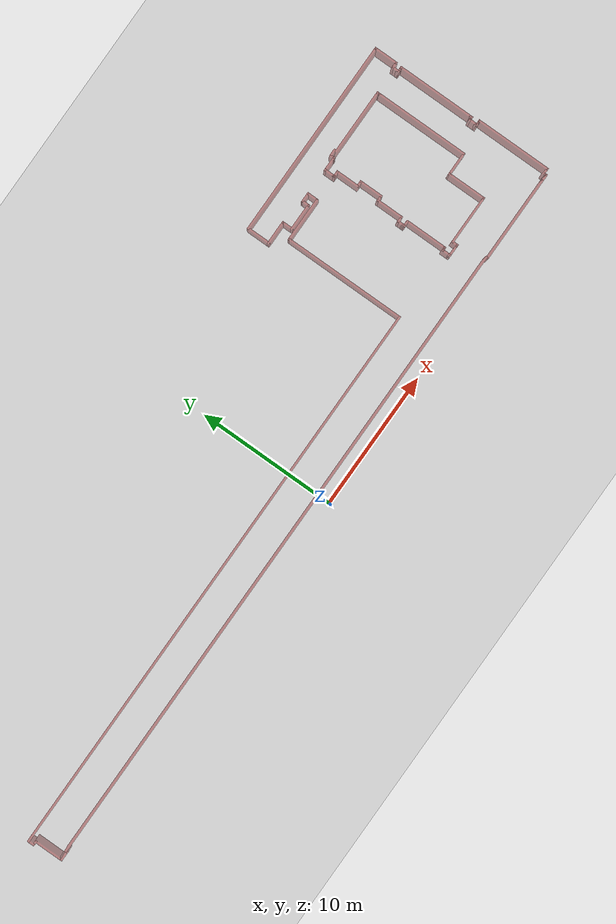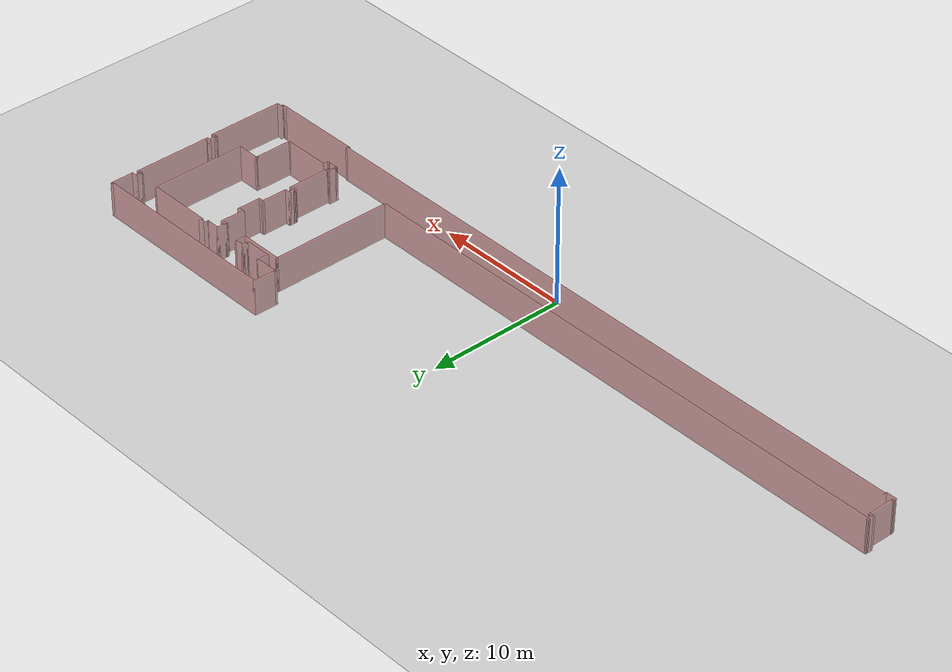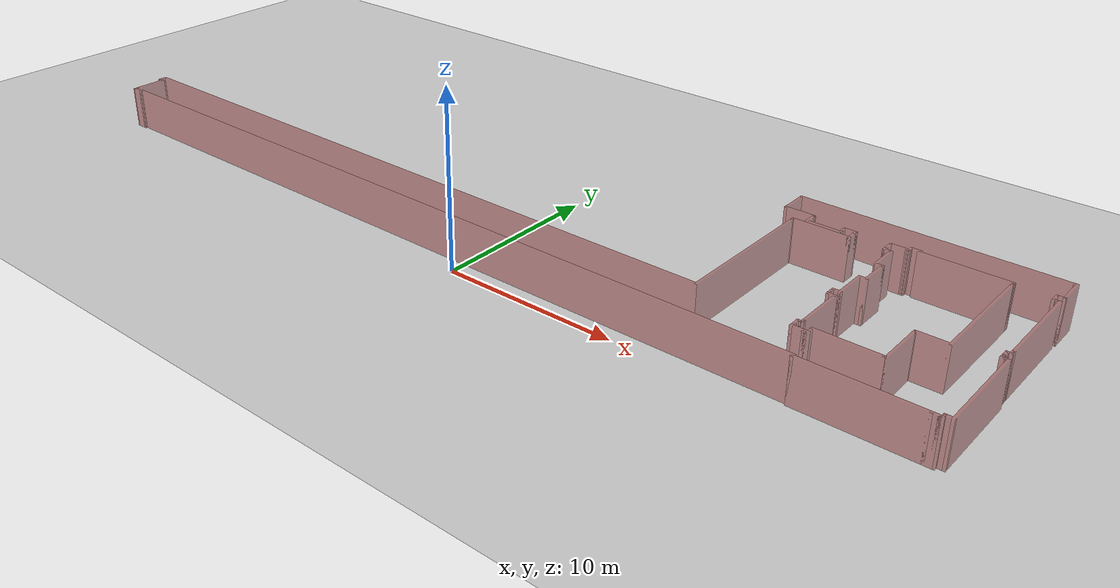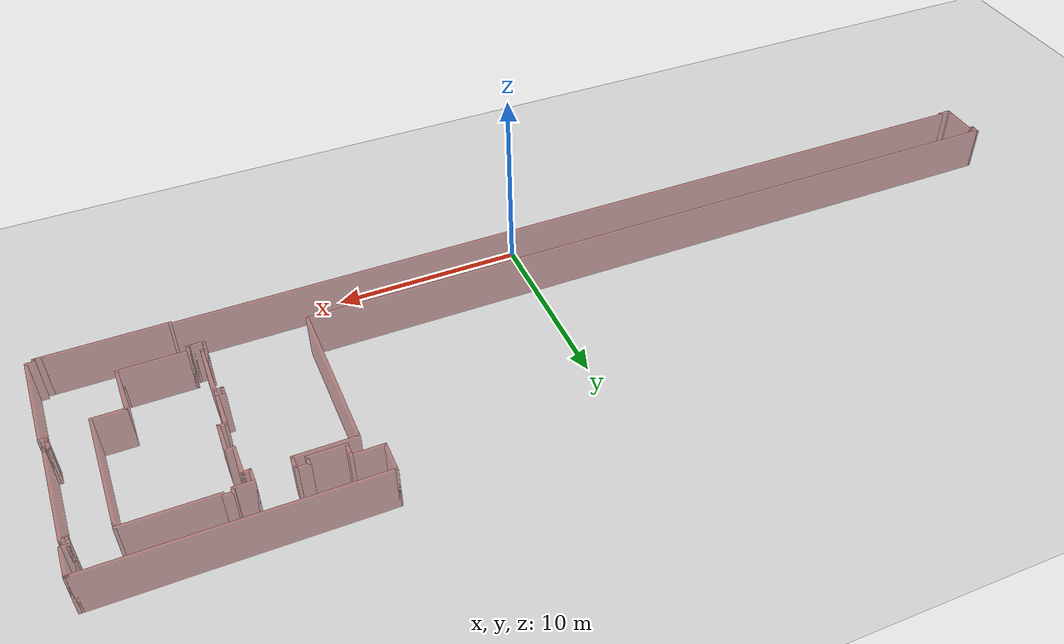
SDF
<sdf version='1.7'>
  <world name='default'>
    <plugin filename="libignition-gazebo-physics-system.so" name="ignition::gazebo::systems::Physics"></plugin>
    <plugin filename="libignition-gazebo-scene-broadcaster-system.so" name="ignition::gazebo::systems::SceneBroadcaster"></plugin>

    <plugin filename="libignition-gazebo-user-commands-system.so" name="ignition::gazebo::systems::UserCommands"></plugin>

    <plugin filename="libignition-gazebo-sensors-system.so" name="ignition::gazebo::systems::Sensors">
        <render_engine>ogre</render_engine>
    </plugin>
    <light name='sun' type='directional'>
      <cast_shadows>true</cast_shadows>
      <pose>0 0 10 0 0 0</pose>
      <diffuse>0.8 0.8 0.8 1</diffuse>
      <specular>0.2 0.2 0.2 1</specular>
      <attenuation>
        <range>1000</range>
        <constant>0.9</constant>
        <linear>0.01</linear>
        <quadratic>0.001</quadratic>
      </attenuation>
      <direction>-0.5 0.1 -0.9</direction>
      <spot>
        <inner_angle>0</inner_angle>
        <outer_angle>0</outer_angle>
        <falloff>0</falloff>
      </spot>
    </light>
    <model name='ground_plane'>
      <static>1</static>
      <link name='link'>
        <collision name='collision'>
          <geometry>
            <plane>
              <normal>0 0 1</normal>
              <size>150 150</size>
            </plane>
          </geometry>
          <surface>
            <contact>
              <collide_bitmask>65535</collide_bitmask>
              <ode/>
            </contact>
            <friction>
              <ode>
                <mu>100</mu>
                <mu2>50</mu2>
              </ode>
              <torsional>
                <ode/>
              </torsional>
            </friction>
            <bounce/>
          </surface>
          <max_contacts>10</max_contacts>
        </collision>
        <visual name='visual'>
          <cast_shadows>0</cast_shadows>
          <geometry>
            <plane>
              <normal>0 0 1</normal>
              <size>100 100</size>
            </plane>
          </geometry>
          <material>
            <ambient>0.8 0.8 0.8 1.0</ambient>
            <diffuse>0.8 0.8 0.8 1.0</diffuse>
            <specular>0.1 0.1 0.1 1.0</specular>
            <pbr>
              <metal>
                <albedo>0.8 0.8 0.8 1.0</albedo>
                <metalness>0.0</metalness>
                <roughness>0.9</roughness>
              </metal>
            </pbr>
          </material>
        </visual>
        <self_collide>0</self_collide>
        <enable_wind>0</enable_wind>
        <kinematic>0</kinematic>
      </link>
    </model>
    <gravity>0 0 -9.8</gravity>
    <magnetic_field>6e-06 2.3e-05 -4.2e-05</magnetic_field>
    <atmosphere type='adiabatic'/>
    <physics type='ode'>
      <max_step_size>0.001</max_step_size>
      <real_time_factor>1</real_time_factor>
      <real_time_update_rate>1000</real_time_update_rate>
    </physics>
    <scene>
      <ambient>0.4 0.4 0.4 1</ambient>
      <background>0.7 0.7 0.7 1</background>
      <shadows>1</shadows>
    </scene>
    <audio>
      <device>default</device>
    </audio>
    <wind/>
    <spherical_coordinates>
      <surface_model>EARTH_WGS84</surface_model>
      <latitude_deg>0</latitude_deg>
      <longitude_deg>0</longitude_deg>
      <elevation>0</elevation>
      <heading_deg>0</heading_deg>
    </spherical_coordinates>
    <model name='acopian_4th_floor'>
      <pose>-1.6204 7.29653 0 0 -0 0</pose>
      <link name='Wall_263'>
        <collision name='Wall_263_Collision'>
          <geometry>
            <box>
              <size>41.5 0.15 2.5</size>
            </box>
          </geometry>
          <pose>0 0 1.25 0 -0 0</pose>
          <max_contacts>10</max_contacts>
          <surface>
            <contact>
              <ode/>
            </contact>
            <bounce/>
            <friction>
              <torsional>
                <ode/>
              </torsional>
              <ode/>
            </friction>
          </surface>
        </collision>
        <visual name='Wall_263_Visual'>
          <pose>0 0 1.25 0 -0 0</pose>
          <geometry>
            <box>
              <size>41.5 0.15 2.5</size>
            </box>
          </geometry>
          <material>
            <ambient>0.5 0.0 0.0 0.4</ambient>
            <diffuse>0.5 0.0 0.0 0.4</diffuse>
            <specular>0.1 0.1 0.1 0.4</specular>
            <pbr>
              <metal>
                <albedo>0.5 0.0 0.0 0.4</albedo>
                <metalness>0.1</metalness>
                <roughness>0.8</roughness>
              </metal>
            </pbr>
          </material>
          <meta>
            <layer>0</layer>
          </meta>
        </visual>
        <pose>-6.64974 -4.02847 0 0 -0 3.14159</pose>
        <self_collide>0</self_collide>
        <enable_wind>0</enable_wind>
        <kinematic>0</kinematic>
      </link>
      <link name='Wall_267'>
        <collision name='Wall_267_Collision'>
          <geometry>
            <box>
              <size>8.75 0.15 2.5</size>
            </box>
          </geometry>
          <pose>0 0 1.25 0 -0 0</pose>
          <max_contacts>10</max_contacts>
          <surface>
            <contact>
              <ode/>
            </contact>
            <bounce/>
            <friction>
              <torsional>
                <ode/>
              </torsional>
              <ode/>
            </friction>
          </surface>
        </collision>
        <visual name='Wall_267_Visual'>
          <pose>0 0 1.25 0 -0 0</pose>
          <geometry>
            <box>
              <size>8.75 0.15 2.5</size>
            </box>
          </geometry>
          <material>
            <ambient>0.5 0.0 0.0 0.4</ambient>
            <diffuse>0.5 0.0 0.0 0.4</diffuse>
            <specular>0.1 0.1 0.1 0.4</specular>
            <pbr>
              <metal>
                <albedo>0.5 0.0 0.0 0.4</albedo>
                <metalness>0.1</metalness>
                <roughness>0.8</roughness>
              </metal>
            </pbr>
          </material>
          <meta>
            <layer>0</layer>
          </meta>
        </visual>
        <pose>14.0253 0.271527 0 0 -0 1.5708</pose>
        <self_collide>0</self_collide>
        <enable_wind>0</enable_wind>
        <kinematic>0</kinematic>
      </link>
      <link name='Wall_269'>
        <collision name='Wall_269_Collision'>
          <geometry>
            <box>
              <size>0.25 0.15 2.5</size>
            </box>
          </geometry>
          <pose>0 0 1.25 0 -0 0</pose>
          <max_contacts>10</max_contacts>
          <surface>
            <contact>
              <ode/>
            </contact>
            <bounce/>
            <friction>
              <torsional>
                <ode/>
              </torsional>
              <ode/>
            </friction>
          </surface>
        </collision>
        <visual name='Wall_269_Visual'>
          <pose>0 0 1.25 0 -0 0</pose>
          <geometry>
            <box>
              <size>0.25 0.15 2.5</size>
            </box>
          </geometry>
          <material>
            <ambient>0.5 0.0 0.0 0.4</ambient>
            <diffuse>0.5 0.0 0.0 0.4</diffuse>
            <specular>0.1 0.1 0.1 0.4</specular>
            <pbr>
              <metal>
                <albedo>0.5 0.0 0.0 0.4</albedo>
                <metalness>0.1</metalness>
                <roughness>0.8</roughness>
              </metal>
            </pbr>
          </material>
          <meta>
            <layer>0</layer>
          </meta>
        </visual>
        <pose>14.0253 4.62153 0 0 -0 1.5708</pose>
        <self_collide>0</self_collide>
        <enable_wind>0</enable_wind>
        <kinematic>0</kinematic>
      </link>
      <link name='Wall_270'>
        <collision name='Wall_270_Collision'>
          <geometry>
            <box>
              <size>3.25 0.15 2.5</size>
            </box>
          </geometry>
          <pose>0 0 1.25 0 -0 0</pose>
          <max_contacts>10</max_contacts>
          <surface>
            <contact>
              <ode/>
            </contact>
            <bounce/>
            <friction>
              <torsional>
                <ode/>
              </torsional>
              <ode/>
            </friction>
          </surface>
        </collision>
        <visual name='Wall_270_Visual'>
          <pose>0 0 1.25 0 -0 0</pose>
          <geometry>
            <box>
              <size>3.25 0.15 2.5</size>
            </box>
          </geometry>
          <material>
            <ambient>0.5 0.0 0.0 0.4</ambient>
            <diffuse>0.5 0.0 0.0 0.4</diffuse>
            <specular>0.1 0.1 0.1 0.4</specular>
            <pbr>
              <metal>
                <albedo>0.5 0.0 0.0 0.4</albedo>
                <metalness>0.1</metalness>
                <roughness>0.8</roughness>
              </metal>
            </pbr>
          </material>
          <meta>
            <layer>0</layer>
          </meta>
        </visual>
        <pose>15.5753 4.67153 0 0 -0 0</pose>
        <self_collide>0</self_collide>
        <enable_wind>0</enable_wind>
        <kinematic>0</kinematic>
      </link>
      <link name='Wall_271'>
        <collision name='Wall_271_Collision'>
          <geometry>
            <box>
              <size>0.75 0.15 2.5</size>
            </box>
          </geometry>
          <pose>0 0 1.25 0 -0 0</pose>
          <max_contacts>10</max_contacts>
          <surface>
            <contact>
              <ode/>
            </contact>
            <bounce/>
            <friction>
              <torsional>
                <ode/>
              </torsional>
              <ode/>
            </friction>
          </surface>
        </collision>
        <visual name='Wall_271_Visual'>
          <pose>0 0 1.25 0 -0 0</pose>
          <geometry>
            <box>
              <size>0.75 0.15 2.5</size>
            </box>
          </geometry>
          <material>
            <ambient>0.5 0.0 0.0 0.4</ambient>
            <diffuse>0.5 0.0 0.0 0.4</diffuse>
            <specular>0.1 0.1 0.1 0.4</specular>
            <pbr>
              <metal>
                <albedo>0.5 0.0 0.0 0.4</albedo>
                <metalness>0.1</metalness>
                <roughness>0.8</roughness>
              </metal>
            </pbr>
          </material>
          <meta>
            <layer>0</layer>
          </meta>
        </visual>
        <pose>17.1253 4.97153 0 0 -0 1.5708</pose>
        <self_collide>0</self_collide>
        <enable_wind>0</enable_wind>
        <kinematic>0</kinematic>
      </link>
      <link name='Wall_272'>
        <collision name='Wall_272_Collision'>
          <geometry>
            <box>
              <size>0.25 0.15 2.5</size>
            </box>
          </geometry>
          <pose>0 0 1.25 0 -0 0</pose>
          <max_contacts>10</max_contacts>
          <surface>
            <contact>
              <ode/>
            </contact>
            <bounce/>
            <friction>
              <torsional>
                <ode/>
              </torsional>
              <ode/>
            </friction>
          </surface>
        </collision>
        <visual name='Wall_272_Visual'>
          <pose>0 0 1.25 0 -0 0</pose>
          <geometry>
            <box>
              <size>0.25 0.15 2.5</size>
            </box>
          </geometry>
          <material>
            <ambient>0.5 0.0 0.0 0.4</ambient>
            <diffuse>0.5 0.0 0.0 0.4</diffuse>
            <specular>0.1 0.1 0.1 0.4</specular>
            <pbr>
              <metal>
                <albedo>0.5 0.0 0.0 0.4</albedo>
                <metalness>0.1</metalness>
                <roughness>0.8</roughness>
              </metal>
            </pbr>
          </material>
          <meta>
            <layer>0</layer>
          </meta>
        </visual>
        <pose>17.1253 5.32153 0 0 -0 1.5708</pose>
        <self_collide>0</self_collide>
        <enable_wind>0</enable_wind>
        <kinematic>0</kinematic>
      </link>
      <link name='Wall_273'>
        <collision name='Wall_273_Collision'>
          <geometry>
            <box>
              <size>0.75 0.15 2.5</size>
            </box>
          </geometry>
          <pose>0 0 1.25 0 -0 0</pose>
          <max_contacts>10</max_contacts>
          <surface>
            <contact>
              <ode/>
            </contact>
            <bounce/>
            <friction>
              <torsional>
                <ode/>
              </torsional>
              <ode/>
            </friction>
          </surface>
        </collision>
        <visual name='Wall_273_Visual'>
          <pose>0 0 1.25 0 -0 0</pose>
          <geometry>
            <box>
              <size>0.75 0.15 2.5</size>
            </box>
          </geometry>
          <material>
            <ambient>0.5 0.0 0.0 0.4</ambient>
            <diffuse>0.5 0.0 0.0 0.4</diffuse>
            <specular>0.1 0.1 0.1 0.4</specular>
            <pbr>
              <metal>
                <albedo>0.5 0.0 0.0 0.4</albedo>
                <metalness>0.1</metalness>
                <roughness>0.8</roughness>
              </metal>
            </pbr>
          </material>
          <meta>
            <layer>0</layer>
          </meta>
        </visual>
        <pose>16.8253 5.37153 0 0 -0 3.14159</pose>
        <self_collide>0</self_collide>
        <enable_wind>0</enable_wind>
        <kinematic>0</kinematic>
      </link>
      <link name='Wall_274'>
        <collision name='Wall_274_Collision'>
          <geometry>
            <box>
              <size>0.5 0.15 2.5</size>
            </box>
          </geometry>
          <pose>0 0 1.25 0 -0 0</pose>
          <max_contacts>10</max_contacts>
          <surface>
            <contact>
              <ode/>
            </contact>
            <bounce/>
            <friction>
              <torsional>
                <ode/>
              </torsional>
              <ode/>
            </friction>
          </surface>
        </collision>
        <visual name='Wall_274_Visual'>
          <pose>0 0 1.25 0 -0 0</pose>
          <geometry>
            <box>
              <size>0.5 0.15 2.5</size>
            </box>
          </geometry>
          <material>
            <ambient>0.5 0.0 0.0 0.4</ambient>
            <diffuse>0.5 0.0 0.0 0.4</diffuse>
            <specular>0.1 0.1 0.1 0.4</specular>
            <pbr>
              <metal>
                <albedo>0.5 0.0 0.0 0.4</albedo>
                <metalness>0.1</metalness>
                <roughness>0.8</roughness>
              </metal>
            </pbr>
          </material>
          <meta>
            <layer>0</layer>
          </meta>
        </visual>
        <pose>16.5253 5.19653 0 0 -0 -1.5708</pose>
        <self_collide>0</self_collide>
        <enable_wind>0</enable_wind>
        <kinematic>0</kinematic>
      </link>
      <link name='Wall_275'>
        <collision name='Wall_275_Collision'>
          <geometry>
            <box>
              <size>0.25 0.15 2.5</size>
            </box>
          </geometry>
          <pose>0 0 1.25 0 -0 0</pose>
          <max_contacts>10</max_contacts>
          <surface>
            <contact>
              <ode/>
            </contact>
            <bounce/>
            <friction>
              <torsional>
                <ode/>
              </torsional>
              <ode/>
            </friction>
          </surface>
        </collision>
        <visual name='Wall_275_Visual'>
          <pose>0 0 1.25 0 -0 0</pose>
          <geometry>
            <box>
              <size>0.25 0.15 2.5</size>
            </box>
          </geometry>
          <material>
            <ambient>0.5 0.0 0.0 0.4</ambient>
            <diffuse>0.5 0.0 0.0 0.4</diffuse>
            <specular>0.1 0.1 0.1 0.4</specular>
            <pbr>
              <metal>
                <albedo>0.5 0.0 0.0 0.4</albedo>
                <metalness>0.1</metalness>
                <roughness>0.8</roughness>
              </metal>
            </pbr>
          </material>
          <meta>
            <layer>0</layer>
          </meta>
        </visual>
        <pose>16.5253 4.97153 0 0 -0 -1.5708</pose>
        <self_collide>0</self_collide>
        <enable_wind>0</enable_wind>
        <kinematic>0</kinematic>
      </link>
      <link name='Wall_276'>
        <collision name='Wall_276_Collision'>
          <geometry>
            <box>
              <size>2 0.15 2.5</size>
            </box>
          </geometry>
          <pose>0 0 1.25 0 -0 0</pose>
          <max_contacts>10</max_contacts>
          <surface>
            <contact>
              <ode/>
            </contact>
            <bounce/>
            <friction>
              <torsional>
                <ode/>
              </torsional>
              <ode/>
            </friction>
          </surface>
        </collision>
        <visual name='Wall_276_Visual'>
          <pose>0 0 1.25 0 -0 0</pose>
          <geometry>
            <box>
              <size>2 0.15 2.5</size>
            </box>
          </geometry>
          <material>
            <ambient>0.5 0.0 0.0 0.4</ambient>
            <diffuse>0.5 0.0 0.0 0.4</diffuse>
            <specular>0.1 0.1 0.1 0.4</specular>
            <pbr>
              <metal>
                <albedo>0.5 0.0 0.0 0.4</albedo>
                <metalness>0.1</metalness>
                <roughness>0.8</roughness>
              </metal>
            </pbr>
          </material>
          <meta>
            <layer>0</layer>
          </meta>
        </visual>
        <pose>15.6003 4.92153 0 0 -0 3.14159</pose>
        <self_collide>0</self_collide>
        <enable_wind>0</enable_wind>
        <kinematic>0</kinematic>
      </link>
      <link name='Wall_277'>
        <collision name='Wall_277_Collision'>
          <geometry>
            <box>
              <size>0.75 0.15 2.5</size>
            </box>
          </geometry>
          <pose>0 0 1.25 0 -0 0</pose>
          <max_contacts>10</max_contacts>
          <surface>
            <contact>
              <ode/>
            </contact>
            <bounce/>
            <friction>
              <torsional>
                <ode/>
              </torsional>
              <ode/>
            </friction>
          </surface>
        </collision>
        <visual name='Wall_277_Visual'>
          <pose>0 0 1.25 0 -0 0</pose>
          <geometry>
            <box>
              <size>0.75 0.15 2.5</size>
            </box>
          </geometry>
          <material>
            <ambient>0.5 0.0 0.0 0.4</ambient>
            <diffuse>0.5 0.0 0.0 0.4</diffuse>
            <specular>0.1 0.1 0.1 0.4</specular>
            <pbr>
              <metal>
                <albedo>0.5 0.0 0.0 0.4</albedo>
                <metalness>0.1</metalness>
                <roughness>0.8</roughness>
              </metal>
            </pbr>
          </material>
          <meta>
            <layer>0</layer>
          </meta>
        </visual>
        <pose>14.6753 5.22153 0 0 -0 1.5708</pose>
        <self_collide>0</self_collide>
        <enable_wind>0</enable_wind>
        <kinematic>0</kinematic>
      </link>
      <link name='Wall_278'>
        <collision name='Wall_278_Collision'>
          <geometry>
            <box>
              <size>0.25 0.15 2.5</size>
            </box>
          </geometry>
          <pose>0 0 1.25 0 -0 0</pose>
          <max_contacts>10</max_contacts>
          <surface>
            <contact>
              <ode/>
            </contact>
            <bounce/>
            <friction>
              <torsional>
                <ode/>
              </torsional>
              <ode/>
            </friction>
          </surface>
        </collision>
        <visual name='Wall_278_Visual'>
          <pose>0 0 1.25 0 -0 0</pose>
          <geometry>
            <box>
              <size>0.25 0.15 2.5</size>
            </box>
          </geometry>
          <material>
            <ambient>0.5 0.0 0.0 0.4</ambient>
            <diffuse>0.5 0.0 0.0 0.4</diffuse>
            <specular>0.1 0.1 0.1 0.4</specular>
            <pbr>
              <metal>
                <albedo>0.5 0.0 0.0 0.4</albedo>
                <metalness>0.1</metalness>
                <roughness>0.8</roughness>
              </metal>
            </pbr>
          </material>
          <meta>
            <layer>0</layer>
          </meta>
        </visual>
        <pose>14.6753 5.57153 0 0 -0 1.5708</pose>
        <self_collide>0</self_collide>
        <enable_wind>0</enable_wind>
        <kinematic>0</kinematic>
      </link>
      <link name='Wall_279'>
        <collision name='Wall_279_Collision'>
          <geometry>
            <box>
              <size>1.75 0.15 2.5</size>
            </box>
          </geometry>
          <pose>0 0 1.25 0 -0 0</pose>
          <max_contacts>10</max_contacts>
          <surface>
            <contact>
              <ode/>
            </contact>
            <bounce/>
            <friction>
              <torsional>
                <ode/>
              </torsional>
              <ode/>
            </friction>
          </surface>
        </collision>
        <visual name='Wall_279_Visual'>
          <pose>0 0 1.25 0 -0 0</pose>
          <geometry>
            <box>
              <size>1.75 0.15 2.5</size>
            </box>
          </geometry>
          <material>
            <ambient>0.5 0.0 0.0 0.4</ambient>
            <diffuse>0.5 0.0 0.0 0.4</diffuse>
            <specular>0.1 0.1 0.1 0.4</specular>
            <pbr>
              <metal>
                <albedo>0.5 0.0 0.0 0.4</albedo>
                <metalness>0.1</metalness>
                <roughness>0.8</roughness>
              </metal>
            </pbr>
          </material>
          <meta>
            <layer>0</layer>
          </meta>
        </visual>
        <pose>13.8753 5.62153 0 0 -0 3.14159</pose>
        <self_collide>0</self_collide>
        <enable_wind>0</enable_wind>
        <kinematic>0</kinematic>
      </link>
      <link name='Wall_281'>
        <collision name='Wall_281_Collision'>
          <geometry>
            <box>
              <size>1.75 0.15 2.5</size>
            </box>
          </geometry>
          <pose>0 0 1.25 0 -0 0</pose>
          <max_contacts>10</max_contacts>
          <surface>
            <contact>
              <ode/>
            </contact>
            <bounce/>
            <friction>
              <torsional>
                <ode/>
              </torsional>
              <ode/>
            </friction>
          </surface>
        </collision>
        <visual name='Wall_281_Visual'>
          <pose>0 0 1.25 0 -0 0</pose>
          <geometry>
            <box>
              <size>1.75 0.15 2.5</size>
            </box>
          </geometry>
          <material>
            <ambient>0.5 0.0 0.0 0.4</ambient>
            <diffuse>0.5 0.0 0.0 0.4</diffuse>
            <specular>0.1 0.1 0.1 0.4</specular>
            <pbr>
              <metal>
                <albedo>0.5 0.0 0.0 0.4</albedo>
                <metalness>0.1</metalness>
                <roughness>0.8</roughness>
              </metal>
            </pbr>
          </material>
          <meta>
            <layer>0</layer>
          </meta>
        </visual>
        <pose>13.0753 6.42153 0 0 -0 1.5708</pose>
        <self_collide>0</self_collide>
        <enable_wind>0</enable_wind>
        <kinematic>0</kinematic>
      </link>
      <link name='Wall_284'>
        <collision name='Wall_284_Collision'>
          <geometry>
            <box>
              <size>14.25 0.15 2.5</size>
            </box>
          </geometry>
          <pose>0 0 1.25 0 -0 0</pose>
          <max_contacts>10</max_contacts>
          <surface>
            <contact>
              <ode/>
            </contact>
            <bounce/>
            <friction>
              <torsional>
                <ode/>
              </torsional>
              <ode/>
            </friction>
          </surface>
        </collision>
        <visual name='Wall_284_Visual'>
          <pose>0 0 1.25 0 -0 0</pose>
          <geometry>
            <box>
              <size>14.25 0.15 2.5</size>
            </box>
          </geometry>
          <material>
            <ambient>0.5 0.0 0.0 0.4</ambient>
            <diffuse>0.5 0.0 0.0 0.4</diffuse>
            <specular>0.1 0.1 0.1 0.4</specular>
            <pbr>
              <metal>
                <albedo>0.5 0.0 0.0 0.4</albedo>
                <metalness>0.1</metalness>
                <roughness>0.8</roughness>
              </metal>
            </pbr>
          </material>
          <meta>
            <layer>0</layer>
          </meta>
        </visual>
        <pose>20.1253 7.22153 0 0 -0 0</pose>
        <self_collide>0</self_collide>
        <enable_wind>0</enable_wind>
        <kinematic>0</kinematic>
      </link>
      <link name='Wall_288'>
        <collision name='Wall_288_Collision'>
          <geometry>
            <box>
              <size>0.25 0.15 2.5</size>
            </box>
          </geometry>
          <pose>0 0 1.25 0 -0 0</pose>
          <max_contacts>10</max_contacts>
          <surface>
            <contact>
              <ode/>
            </contact>
            <bounce/>
            <friction>
              <torsional>
                <ode/>
              </torsional>
              <ode/>
            </friction>
          </surface>
        </collision>
        <visual name='Wall_288_Visual'>
          <pose>0 0 1.25 0 -0 0</pose>
          <geometry>
            <box>
              <size>0.25 0.15 2.5</size>
            </box>
          </geometry>
          <material>
            <ambient>0.5 0.0 0.0 0.4</ambient>
            <diffuse>0.5 0.0 0.0 0.4</diffuse>
            <specular>0.1 0.1 0.1 0.4</specular>
            <pbr>
              <metal>
                <albedo>0.5 0.0 0.0 0.4</albedo>
                <metalness>0.1</metalness>
                <roughness>0.8</roughness>
              </metal>
            </pbr>
          </material>
          <meta>
            <layer>0</layer>
          </meta>
        </visual>
        <pose>27.2253 7.22153 0 0 -0 0</pose>
        <self_collide>0</self_collide>
        <enable_wind>0</enable_wind>
        <kinematic>0</kinematic>
      </link>
      <link name='Wall_289'>
        <collision name='Wall_289_Collision'>
          <geometry>
            <box>
              <size>1.75 0.15 2.5</size>
            </box>
          </geometry>
          <pose>0 0 1.25 0 -0 0</pose>
          <max_contacts>10</max_contacts>
          <surface>
            <contact>
              <ode/>
            </contact>
            <bounce/>
            <friction>
              <torsional>
                <ode/>
              </torsional>
              <ode/>
            </friction>
          </surface>
        </collision>
        <visual name='Wall_289_Visual'>
          <pose>0 0 1.25 0 -0 0</pose>
          <geometry>
            <box>
              <size>1.75 0.15 2.5</size>
            </box>
          </geometry>
          <material>
            <ambient>0.5 0.0 0.0 0.4</ambient>
            <diffuse>0.5 0.0 0.0 0.4</diffuse>
            <specular>0.1 0.1 0.1 0.4</specular>
            <pbr>
              <metal>
                <albedo>0.5 0.0 0.0 0.4</albedo>
                <metalness>0.1</metalness>
                <roughness>0.8</roughness>
              </metal>
            </pbr>
          </material>
          <meta>
            <layer>0</layer>
          </meta>
        </visual>
        <pose>27.2753 6.42153 0 0 -0 -1.5708</pose>
        <self_collide>0</self_collide>
        <enable_wind>0</enable_wind>
        <kinematic>0</kinematic>
      </link>
      <link name='Wall_294'>
        <collision name='Wall_294_Collision'>
          <geometry>
            <box>
              <size>0.5 0.15 2.5</size>
            </box>
          </geometry>
          <pose>0 0 1.25 0 -0 0</pose>
          <max_contacts>10</max_contacts>
          <surface>
            <contact>
              <ode/>
            </contact>
            <bounce/>
            <friction>
              <torsional>
                <ode/>
              </torsional>
              <ode/>
            </friction>
          </surface>
        </collision>
        <visual name='Wall_294_Visual'>
          <pose>0 0 1.25 0 -0 0</pose>
          <geometry>
            <box>
              <size>0.5 0.15 2.5</size>
            </box>
          </geometry>
          <material>
            <ambient>0.5 0.0 0.0 0.4</ambient>
            <diffuse>0.5 0.0 0.0 0.4</diffuse>
            <specular>0.1 0.1 0.1 0.4</specular>
            <pbr>
              <metal>
                <albedo>0.5 0.0 0.0 0.4</albedo>
                <metalness>0.1</metalness>
                <roughness>0.8</roughness>
              </metal>
            </pbr>
          </material>
          <meta>
            <layer>0</layer>
          </meta>
        </visual>
        <pose>27.1003 5.62153 0 0 -0 3.14159</pose>
        <self_collide>0</self_collide>
        <enable_wind>0</enable_wind>
        <kinematic>0</kinematic>
      </link>
      <link name='Wall_295'>
        <collision name='Wall_295_Collision'>
          <geometry>
            <box>
              <size>0.5 0.15 2.5</size>
            </box>
          </geometry>
          <pose>0 0 1.25 0 -0 0</pose>
          <max_contacts>10</max_contacts>
          <surface>
            <contact>
              <ode/>
            </contact>
            <bounce/>
            <friction>
              <torsional>
                <ode/>
              </torsional>
              <ode/>
            </friction>
          </surface>
        </collision>
        <visual name='Wall_295_Visual'>
          <pose>0 0 1.25 0 -0 0</pose>
          <geometry>
            <box>
              <size>0.5 0.15 2.5</size>
            </box>
          </geometry>
          <material>
            <ambient>0.5 0.0 0.0 0.4</ambient>
            <diffuse>0.5 0.0 0.0 0.4</diffuse>
            <specular>0.1 0.1 0.1 0.4</specular>
            <pbr>
              <metal>
                <albedo>0.5 0.0 0.0 0.4</albedo>
                <metalness>0.1</metalness>
                <roughness>0.8</roughness>
              </metal>
            </pbr>
          </material>
          <meta>
            <layer>0</layer>
          </meta>
        </visual>
        <pose>26.9253 5.44653 0 0 -0 -1.5708</pose>
        <self_collide>0</self_collide>
        <enable_wind>0</enable_wind>
        <kinematic>0</kinematic>
      </link>
      <link name='Wall_300'>
        <collision name='Wall_300_Collision'>
          <geometry>
            <box>
              <size>0.25 0.15 2.5</size>
            </box>
          </geometry>
          <pose>0 0 1.25 0 -0 0</pose>
          <max_contacts>10</max_contacts>
          <surface>
            <contact>
              <ode/>
            </contact>
            <bounce/>
            <friction>
              <torsional>
                <ode/>
              </torsional>
              <ode/>
            </friction>
          </surface>
        </collision>
        <visual name='Wall_300_Visual'>
          <pose>0 0 1.25 0 -0 0</pose>
          <geometry>
            <box>
              <size>0.25 0.15 2.5</size>
            </box>
          </geometry>
          <material>
            <ambient>0.5 0.0 0.0 0.4</ambient>
            <diffuse>0.5 0.0 0.0 0.4</diffuse>
            <specular>0.1 0.1 0.1 0.4</specular>
            <pbr>
              <metal>
                <albedo>0.5 0.0 0.0 0.4</albedo>
                <metalness>0.1</metalness>
                <roughness>0.8</roughness>
              </metal>
            </pbr>
          </material>
          <meta>
            <layer>0</layer>
          </meta>
        </visual>
        <pose>26.9253 5.22153 0 0 -0 -1.5708</pose>
        <self_collide>0</self_collide>
        <enable_wind>0</enable_wind>
        <kinematic>0</kinematic>
      </link>
      <link name='Wall_301'>
        <collision name='Wall_301_Collision'>
          <geometry>
            <box>
              <size>0.25 0.15 2.5</size>
            </box>
          </geometry>
          <pose>0 0 1.25 0 -0 0</pose>
          <max_contacts>10</max_contacts>
          <surface>
            <contact>
              <ode/>
            </contact>
            <bounce/>
            <friction>
              <torsional>
                <ode/>
              </torsional>
              <ode/>
            </friction>
          </surface>
        </collision>
        <visual name='Wall_301_Visual'>
          <pose>0 0 1.25 0 -0 0</pose>
          <geometry>
            <box>
              <size>0.25 0.15 2.5</size>
            </box>
          </geometry>
          <material>
            <ambient>0.5 0.0 0.0 0.4</ambient>
            <diffuse>0.5 0.0 0.0 0.4</diffuse>
            <specular>0.1 0.1 0.1 0.4</specular>
            <pbr>
              <metal>
                <albedo>0.5 0.0 0.0 0.4</albedo>
                <metalness>0.1</metalness>
                <roughness>0.8</roughness>
              </metal>
            </pbr>
          </material>
          <meta>
            <layer>0</layer>
          </meta>
        </visual>
        <pose>26.9753 5.17153 0 0 -0 0</pose>
        <self_collide>0</self_collide>
        <enable_wind>0</enable_wind>
        <kinematic>0</kinematic>
      </link>
      <link name='Wall_302'>
        <collision name='Wall_302_Collision'>
          <geometry>
            <box>
              <size>0.25 0.15 2.5</size>
            </box>
          </geometry>
          <pose>0 0 1.25 0 -0 0</pose>
          <max_contacts>10</max_contacts>
          <surface>
            <contact>
              <ode/>
            </contact>
            <bounce/>
            <friction>
              <torsional>
                <ode/>
              </torsional>
              <ode/>
            </friction>
          </surface>
        </collision>
        <visual name='Wall_302_Visual'>
          <pose>0 0 1.25 0 -0 0</pose>
          <geometry>
            <box>
              <size>0.25 0.15 2.5</size>
            </box>
          </geometry>
          <material>
            <ambient>0.5 0.0 0.0 0.4</ambient>
            <diffuse>0.5 0.0 0.0 0.4</diffuse>
            <specular>0.1 0.1 0.1 0.4</specular>
            <pbr>
              <metal>
                <albedo>0.5 0.0 0.0 0.4</albedo>
                <metalness>0.1</metalness>
                <roughness>0.8</roughness>
              </metal>
            </pbr>
          </material>
          <meta>
            <layer>0</layer>
          </meta>
        </visual>
        <pose>27.0753 5.17153 0 0 -0 0</pose>
        <self_collide>0</self_collide>
        <enable_wind>0</enable_wind>
        <kinematic>0</kinematic>
      </link>
      <link name='Wall_303'>
        <collision name='Wall_303_Collision'>
          <geometry>
            <box>
              <size>0.25 0.15 2.5</size>
            </box>
          </geometry>
          <pose>0 0 1.25 0 -0 0</pose>
          <max_contacts>10</max_contacts>
          <surface>
            <contact>
              <ode/>
            </contact>
            <bounce/>
            <friction>
              <torsional>
                <ode/>
              </torsional>
              <ode/>
            </friction>
          </surface>
        </collision>
        <visual name='Wall_303_Visual'>
          <pose>0 0 1.25 0 -0 0</pose>
          <geometry>
            <box>
              <size>0.25 0.15 2.5</size>
            </box>
          </geometry>
          <material>
            <ambient>0.5 0.0 0.0 0.4</ambient>
            <diffuse>0.5 0.0 0.0 0.4</diffuse>
            <specular>0.1 0.1 0.1 0.4</specular>
            <pbr>
              <metal>
                <albedo>0.5 0.0 0.0 0.4</albedo>
                <metalness>0.1</metalness>
                <roughness>0.8</roughness>
              </metal>
            </pbr>
          </material>
          <meta>
            <layer>0</layer>
          </meta>
        </visual>
        <pose>27.1753 5.17153 0 0 -0 0</pose>
        <self_collide>0</self_collide>
        <enable_wind>0</enable_wind>
        <kinematic>0</kinematic>
      </link>
      <link name='Wall_304'>
        <collision name='Wall_304_Collision'>
          <geometry>
            <box>
              <size>5.5 0.15 2.5</size>
            </box>
          </geometry>
          <pose>0 0 1.25 0 -0 0</pose>
          <max_contacts>10</max_contacts>
          <surface>
            <contact>
              <ode/>
            </contact>
            <bounce/>
            <friction>
              <torsional>
                <ode/>
              </torsional>
              <ode/>
            </friction>
          </surface>
        </collision>
        <visual name='Wall_304_Visual'>
          <pose>0 0 1.25 0 -0 0</pose>
          <geometry>
            <box>
              <size>5.5 0.15 2.5</size>
            </box>
          </geometry>
          <material>
            <ambient>0.5 0.0 0.0 0.4</ambient>
            <diffuse>0.5 0.0 0.0 0.4</diffuse>
            <specular>0.1 0.1 0.1 0.4</specular>
            <pbr>
              <metal>
                <albedo>0.5 0.0 0.0 0.4</albedo>
                <metalness>0.1</metalness>
                <roughness>0.8</roughness>
              </metal>
            </pbr>
          </material>
          <meta>
            <layer>0</layer>
          </meta>
        </visual>
        <pose>27.2253 2.49653 0 0 -0 -1.5708</pose>
        <self_collide>0</self_collide>
        <enable_wind>0</enable_wind>
        <kinematic>0</kinematic>
      </link>
      <link name='Wall_306'>
        <collision name='Wall_306_Collision'>
          <geometry>
            <box>
              <size>0.25 0.15 2.5</size>
            </box>
          </geometry>
          <pose>0 0 1.25 0 -0 0</pose>
          <max_contacts>10</max_contacts>
          <surface>
            <contact>
              <ode/>
            </contact>
            <bounce/>
            <friction>
              <torsional>
                <ode/>
              </torsional>
              <ode/>
            </friction>
          </surface>
        </collision>
        <visual name='Wall_306_Visual'>
          <pose>0 0 1.25 0 -0 0</pose>
          <geometry>
            <box>
              <size>0.25 0.15 2.5</size>
            </box>
          </geometry>
          <material>
            <ambient>0.5 0.0 0.0 0.4</ambient>
            <diffuse>0.5 0.0 0.0 0.4</diffuse>
            <specular>0.1 0.1 0.1 0.4</specular>
            <pbr>
              <metal>
                <albedo>0.5 0.0 0.0 0.4</albedo>
                <metalness>0.1</metalness>
                <roughness>0.8</roughness>
              </metal>
            </pbr>
          </material>
          <meta>
            <layer>0</layer>
          </meta>
        </visual>
        <pose>27.2253 -0.228473 0 0 -0 -1.5708</pose>
        <self_collide>0</self_collide>
        <enable_wind>0</enable_wind>
        <kinematic>0</kinematic>
      </link>
      <link name='Wall_307'>
        <collision name='Wall_307_Collision'>
          <geometry>
            <box>
              <size>0.25 0.15 2.5</size>
            </box>
          </geometry>
          <pose>0 0 1.25 0 -0 0</pose>
          <max_contacts>10</max_contacts>
          <surface>
            <contact>
              <ode/>
            </contact>
            <bounce/>
            <friction>
              <torsional>
                <ode/>
              </torsional>
              <ode/>
            </friction>
          </surface>
        </collision>
        <visual name='Wall_307_Visual'>
          <pose>0 0 1.25 0 -0 0</pose>
          <geometry>
            <box>
              <size>0.25 0.15 2.5</size>
            </box>
          </geometry>
          <material>
            <ambient>0.5 0.0 0.0 0.4</ambient>
            <diffuse>0.5 0.0 0.0 0.4</diffuse>
            <specular>0.1 0.1 0.1 0.4</specular>
            <pbr>
              <metal>
                <albedo>0.5 0.0 0.0 0.4</albedo>
                <metalness>0.1</metalness>
                <roughness>0.8</roughness>
              </metal>
            </pbr>
          </material>
          <meta>
            <layer>0</layer>
          </meta>
        </visual>
        <pose>27.2253 -0.328473 0 0 -0 -1.5708</pose>
        <self_collide>0</self_collide>
        <enable_wind>0</enable_wind>
        <kinematic>0</kinematic>
      </link>
      <link name='Wall_308'>
        <collision name='Wall_308_Collision'>
          <geometry>
            <box>
              <size>0.25 0.15 2.5</size>
            </box>
          </geometry>
          <pose>0 0 1.25 0 -0 0</pose>
          <max_contacts>10</max_contacts>
          <surface>
            <contact>
              <ode/>
            </contact>
            <bounce/>
            <friction>
              <torsional>
                <ode/>
              </torsional>
              <ode/>
            </friction>
          </surface>
        </collision>
        <visual name='Wall_308_Visual'>
          <pose>0 0 1.25 0 -0 0</pose>
          <geometry>
            <box>
              <size>0.25 0.15 2.5</size>
            </box>
          </geometry>
          <material>
            <ambient>0.5 0.0 0.0 0.4</ambient>
            <diffuse>0.5 0.0 0.0 0.4</diffuse>
            <specular>0.1 0.1 0.1 0.4</specular>
            <pbr>
              <metal>
                <albedo>0.5 0.0 0.0 0.4</albedo>
                <metalness>0.1</metalness>
                <roughness>0.8</roughness>
              </metal>
            </pbr>
          </material>
          <meta>
            <layer>0</layer>
          </meta>
        </visual>
        <pose>27.1753 -0.378473 0 0 -0 3.14159</pose>
        <self_collide>0</self_collide>
        <enable_wind>0</enable_wind>
        <kinematic>0</kinematic>
      </link>
      <link name='Wall_309'>
        <collision name='Wall_309_Collision'>
          <geometry>
            <box>
              <size>0.25 0.15 2.5</size>
            </box>
          </geometry>
          <pose>0 0 1.25 0 -0 0</pose>
          <max_contacts>10</max_contacts>
          <surface>
            <contact>
              <ode/>
            </contact>
            <bounce/>
            <friction>
              <torsional>
                <ode/>
              </torsional>
              <ode/>
            </friction>
          </surface>
        </collision>
        <visual name='Wall_309_Visual'>
          <pose>0 0 1.25 0 -0 0</pose>
          <geometry>
            <box>
              <size>0.25 0.15 2.5</size>
            </box>
          </geometry>
          <material>
            <ambient>0.5 0.0 0.0 0.4</ambient>
            <diffuse>0.5 0.0 0.0 0.4</diffuse>
            <specular>0.1 0.1 0.1 0.4</specular>
            <pbr>
              <metal>
                <albedo>0.5 0.0 0.0 0.4</albedo>
                <metalness>0.1</metalness>
                <roughness>0.8</roughness>
              </metal>
            </pbr>
          </material>
          <meta>
            <layer>0</layer>
          </meta>
        </visual>
        <pose>27.0753 -0.378473 0 0 -0 3.14159</pose>
        <self_collide>0</self_collide>
        <enable_wind>0</enable_wind>
        <kinematic>0</kinematic>
      </link>
      <link name='Wall_310'>
        <collision name='Wall_310_Collision'>
          <geometry>
            <box>
              <size>0.5 0.15 2.5</size>
            </box>
          </geometry>
          <pose>0 0 1.25 0 -0 0</pose>
          <max_contacts>10</max_contacts>
          <surface>
            <contact>
              <ode/>
            </contact>
            <bounce/>
            <friction>
              <torsional>
                <ode/>
              </torsional>
              <ode/>
            </friction>
          </surface>
        </collision>
        <visual name='Wall_310_Visual'>
          <pose>0 0 1.25 0 -0 0</pose>
          <geometry>
            <box>
              <size>0.5 0.15 2.5</size>
            </box>
          </geometry>
          <material>
            <ambient>0.5 0.0 0.0 0.4</ambient>
            <diffuse>0.5 0.0 0.0 0.4</diffuse>
            <specular>0.1 0.1 0.1 0.4</specular>
            <pbr>
              <metal>
                <albedo>0.5 0.0 0.0 0.4</albedo>
                <metalness>0.1</metalness>
                <roughness>0.8</roughness>
              </metal>
            </pbr>
          </material>
          <meta>
            <layer>0</layer>
          </meta>
        </visual>
        <pose>27.0253 -0.553473 0 0 -0 -1.5708</pose>
        <self_collide>0</self_collide>
        <enable_wind>0</enable_wind>
        <kinematic>0</kinematic>
      </link>
      <link name='Wall_311'>
        <collision name='Wall_311_Collision'>
          <geometry>
            <box>
              <size>0.25 0.15 2.5</size>
            </box>
          </geometry>
          <pose>0 0 1.25 0 -0 0</pose>
          <max_contacts>10</max_contacts>
          <surface>
            <contact>
              <ode/>
            </contact>
            <bounce/>
            <friction>
              <torsional>
                <ode/>
              </torsional>
              <ode/>
            </friction>
          </surface>
        </collision>
        <visual name='Wall_311_Visual'>
          <pose>0 0 1.25 0 -0 0</pose>
          <geometry>
            <box>
              <size>0.25 0.15 2.5</size>
            </box>
          </geometry>
          <material>
            <ambient>0.5 0.0 0.0 0.4</ambient>
            <diffuse>0.5 0.0 0.0 0.4</diffuse>
            <specular>0.1 0.1 0.1 0.4</specular>
            <pbr>
              <metal>
                <albedo>0.5 0.0 0.0 0.4</albedo>
                <metalness>0.1</metalness>
                <roughness>0.8</roughness>
              </metal>
            </pbr>
          </material>
          <meta>
            <layer>0</layer>
          </meta>
        </visual>
        <pose>27.0253 -0.778473 0 0 -0 -1.5708</pose>
        <self_collide>0</self_collide>
        <enable_wind>0</enable_wind>
        <kinematic>0</kinematic>
      </link>
      <link name='Wall_312'>
        <collision name='Wall_312_Collision'>
          <geometry>
            <box>
              <size>0.25 0.15 2.5</size>
            </box>
          </geometry>
          <pose>0 0 1.25 0 -0 0</pose>
          <max_contacts>10</max_contacts>
          <surface>
            <contact>
              <ode/>
            </contact>
            <bounce/>
            <friction>
              <torsional>
                <ode/>
              </torsional>
              <ode/>
            </friction>
          </surface>
        </collision>
        <visual name='Wall_312_Visual'>
          <pose>0 0 1.25 0 -0 0</pose>
          <geometry>
            <box>
              <size>0.25 0.15 2.5</size>
            </box>
          </geometry>
          <material>
            <ambient>0.5 0.0 0.0 0.4</ambient>
            <diffuse>0.5 0.0 0.0 0.4</diffuse>
            <specular>0.1 0.1 0.1 0.4</specular>
            <pbr>
              <metal>
                <albedo>0.5 0.0 0.0 0.4</albedo>
                <metalness>0.1</metalness>
                <roughness>0.8</roughness>
              </metal>
            </pbr>
          </material>
          <meta>
            <layer>0</layer>
          </meta>
        </visual>
        <pose>27.0253 -0.878473 0 0 -0 -1.5708</pose>
        <self_collide>0</self_collide>
        <enable_wind>0</enable_wind>
        <kinematic>0</kinematic>
      </link>
      <link name='Wall_313'>
        <collision name='Wall_313_Collision'>
          <geometry>
            <box>
              <size>0.25 0.15 2.5</size>
            </box>
          </geometry>
          <pose>0 0 1.25 0 -0 0</pose>
          <max_contacts>10</max_contacts>
          <surface>
            <contact>
              <ode/>
            </contact>
            <bounce/>
            <friction>
              <torsional>
                <ode/>
              </torsional>
              <ode/>
            </friction>
          </surface>
        </collision>
        <visual name='Wall_313_Visual'>
          <pose>0 0 1.25 0 -0 0</pose>
          <geometry>
            <box>
              <size>0.25 0.15 2.5</size>
            </box>
          </geometry>
          <material>
            <ambient>0.5 0.0 0.0 0.4</ambient>
            <diffuse>0.5 0.0 0.0 0.4</diffuse>
            <specular>0.1 0.1 0.1 0.4</specular>
            <pbr>
              <metal>
                <albedo>0.5 0.0 0.0 0.4</albedo>
                <metalness>0.1</metalness>
                <roughness>0.8</roughness>
              </metal>
            </pbr>
          </material>
          <meta>
            <layer>0</layer>
          </meta>
        </visual>
        <pose>27.0753 -0.928473 0 0 -0 0</pose>
        <self_collide>0</self_collide>
        <enable_wind>0</enable_wind>
        <kinematic>0</kinematic>
      </link>
      <link name='Wall_314'>
        <collision name='Wall_314_Collision'>
          <geometry>
            <box>
              <size>0.25 0.15 2.5</size>
            </box>
          </geometry>
          <pose>0 0 1.25 0 -0 0</pose>
          <max_contacts>10</max_contacts>
          <surface>
            <contact>
              <ode/>
            </contact>
            <bounce/>
            <friction>
              <torsional>
                <ode/>
              </torsional>
              <ode/>
            </friction>
          </surface>
        </collision>
        <visual name='Wall_314_Visual'>
          <pose>0 0 1.25 0 -0 0</pose>
          <geometry>
            <box>
              <size>0.25 0.15 2.5</size>
            </box>
          </geometry>
          <material>
            <ambient>0.5 0.0 0.0 0.4</ambient>
            <diffuse>0.5 0.0 0.0 0.4</diffuse>
            <specular>0.1 0.1 0.1 0.4</specular>
            <pbr>
              <metal>
                <albedo>0.5 0.0 0.0 0.4</albedo>
                <metalness>0.1</metalness>
                <roughness>0.8</roughness>
              </metal>
            </pbr>
          </material>
          <meta>
            <layer>0</layer>
          </meta>
        </visual>
        <pose>27.1753 -0.928473 0 0 -0 0</pose>
        <self_collide>0</self_collide>
        <enable_wind>0</enable_wind>
        <kinematic>0</kinematic>
      </link>
      <link name='Wall_315'>
        <collision name='Wall_315_Collision'>
          <geometry>
            <box>
              <size>0.25 0.15 2.5</size>
            </box>
          </geometry>
          <pose>0 0 1.25 0 -0 0</pose>
          <max_contacts>10</max_contacts>
          <surface>
            <contact>
              <ode/>
            </contact>
            <bounce/>
            <friction>
              <torsional>
                <ode/>
              </torsional>
              <ode/>
            </friction>
          </surface>
        </collision>
        <visual name='Wall_315_Visual'>
          <pose>0 0 1.25 0 -0 0</pose>
          <geometry>
            <box>
              <size>0.25 0.15 2.5</size>
            </box>
          </geometry>
          <material>
            <ambient>0.5 0.0 0.0 0.4</ambient>
            <diffuse>0.5 0.0 0.0 0.4</diffuse>
            <specular>0.1 0.1 0.1 0.4</specular>
            <pbr>
              <metal>
                <albedo>0.5 0.0 0.0 0.4</albedo>
                <metalness>0.1</metalness>
                <roughness>0.8</roughness>
              </metal>
            </pbr>
          </material>
          <meta>
            <layer>0</layer>
          </meta>
        </visual>
        <pose>27.2753 -0.928473 0 0 -0 0</pose>
        <self_collide>0</self_collide>
        <enable_wind>0</enable_wind>
        <kinematic>0</kinematic>
      </link>
      <link name='Wall_316'>
        <collision name='Wall_316_Collision'>
          <geometry>
            <box>
              <size>5.49813 0.15 2.5</size>
            </box>
          </geometry>
          <pose>0 0 1.25 0 -0 0</pose>
          <max_contacts>10</max_contacts>
          <surface>
            <contact>
              <ode/>
            </contact>
            <bounce/>
            <friction>
              <torsional>
                <ode/>
              </torsional>
              <ode/>
            </friction>
          </surface>
        </collision>
        <visual name='Wall_316_Visual'>
          <pose>0 0 1.25 0 -0 0</pose>
          <geometry>
            <box>
              <size>5.49813 0.15 2.5</size>
            </box>
          </geometry>
          <material>
            <ambient>0.5 0.0 0.0 0.4</ambient>
            <diffuse>0.5 0.0 0.0 0.4</diffuse>
            <specular>0.1 0.1 0.1 0.4</specular>
            <pbr>
              <metal>
                <albedo>0.5 0.0 0.0 0.4</albedo>
                <metalness>0.1</metalness>
                <roughness>0.8</roughness>
              </metal>
            </pbr>
          </material>
          <meta>
            <layer>0</layer>
          </meta>
        </visual>
        <pose>27.3253 -3.60254 0 0 -0 -1.5708</pose>
        <self_collide>0</self_collide>
        <enable_wind>0</enable_wind>
        <kinematic>0</kinematic>
      </link>
      <link name='Wall_326'>
        <collision name='Wall_326_Collision'>
          <geometry>
            <box>
              <size>47 0.15 2.5</size>
            </box>
          </geometry>
          <pose>0 0 1.25 0 -0 0</pose>
          <max_contacts>10</max_contacts>
          <surface>
            <contact>
              <ode/>
            </contact>
            <bounce/>
            <friction>
              <torsional>
                <ode/>
              </torsional>
              <ode/>
            </friction>
          </surface>
        </collision>
        <visual name='Wall_326_Visual'>
          <pose>0 0 1.25 0 -0 0</pose>
          <geometry>
            <box>
              <size>47 0.15 2.5</size>
            </box>
          </geometry>
          <material>
            <ambient>0.5 0.0 0.0 0.4</ambient>
            <diffuse>0.5 0.0 0.0 0.4</diffuse>
            <specular>0.1 0.1 0.1 0.4</specular>
            <pbr>
              <metal>
                <albedo>0.5 0.0 0.0 0.4</albedo>
                <metalness>0.1</metalness>
                <roughness>0.8</roughness>
              </metal>
            </pbr>
          </material>
          <meta>
            <layer>0</layer>
          </meta>
        </visual>
        <pose>-3.02221 -6.356 0 0 -0 3.14159</pose>
        <self_collide>0</self_collide>
        <enable_wind>0</enable_wind>
        <kinematic>0</kinematic>
      </link>
      <link name='Wall_329'>
        <collision name='Wall_329_Collision'>
          <geometry>
            <box>
              <size>0.25 0.15 2.5</size>
            </box>
          </geometry>
          <pose>0 0 1.25 0 -0 0</pose>
          <max_contacts>10</max_contacts>
          <surface>
            <contact>
              <ode/>
            </contact>
            <bounce/>
            <friction>
              <torsional>
                <ode/>
              </torsional>
              <ode/>
            </friction>
          </surface>
        </collision>
        <visual name='Wall_329_Visual'>
          <pose>0 0 1.25 0 -0 0</pose>
          <geometry>
            <box>
              <size>0.25 0.15 2.5</size>
            </box>
          </geometry>
          <material>
            <ambient>0.5 0.0 0.0 0.4</ambient>
            <diffuse>0.5 0.0 0.0 0.4</diffuse>
            <specular>0.1 0.1 0.1 0.4</specular>
            <pbr>
              <metal>
                <albedo>0.5 0.0 0.0 0.4</albedo>
                <metalness>0.1</metalness>
                <roughness>0.8</roughness>
              </metal>
            </pbr>
          </material>
          <meta>
            <layer>0</layer>
          </meta>
        </visual>
        <pose>20.4028 -6.406 0 0 -0 -1.5708</pose>
        <self_collide>0</self_collide>
        <enable_wind>0</enable_wind>
        <kinematic>0</kinematic>
      </link>
      <link name='Wall_330'>
        <collision name='Wall_330_Collision'>
          <geometry>
            <box>
              <size>6.25 0.15 2.5</size>
            </box>
          </geometry>
          <pose>0 0 1.25 0 -0 0</pose>
          <max_contacts>10</max_contacts>
          <surface>
            <contact>
              <ode/>
            </contact>
            <bounce/>
            <friction>
              <torsional>
                <ode/>
              </torsional>
              <ode/>
            </friction>
          </surface>
        </collision>
        <visual name='Wall_330_Visual'>
          <pose>0 0 1.25 0 -0 0</pose>
          <geometry>
            <box>
              <size>6.25 0.15 2.5</size>
            </box>
          </geometry>
          <material>
            <ambient>0.5 0.0 0.0 0.4</ambient>
            <diffuse>0.5 0.0 0.0 0.4</diffuse>
            <specular>0.1 0.1 0.1 0.4</specular>
            <pbr>
              <metal>
                <albedo>0.5 0.0 0.0 0.4</albedo>
                <metalness>0.1</metalness>
                <roughness>0.8</roughness>
              </metal>
            </pbr>
          </material>
          <meta>
            <layer>0</layer>
          </meta>
        </visual>
        <pose>23.4528 -6.456 0 0 -0 0</pose>
        <self_collide>0</self_collide>
        <enable_wind>0</enable_wind>
        <kinematic>0</kinematic>
      </link>
      <link name='Wall_334'>
        <collision name='Wall_334_Collision'>
          <geometry>
            <box>
              <size>0.5 0.15 2.5</size>
            </box>
          </geometry>
          <pose>0 0 1.25 0 -0 0</pose>
          <max_contacts>10</max_contacts>
          <surface>
            <contact>
              <ode/>
            </contact>
            <bounce/>
            <friction>
              <torsional>
                <ode/>
              </torsional>
              <ode/>
            </friction>
          </surface>
        </collision>
        <visual name='Wall_334_Visual'>
          <pose>0 0 1.25 0 -0 0</pose>
          <geometry>
            <box>
              <size>0.5 0.15 2.5</size>
            </box>
          </geometry>
          <material>
            <ambient>0.5 0.0 0.0 0.4</ambient>
            <diffuse>0.5 0.0 0.0 0.4</diffuse>
            <specular>0.1 0.1 0.1 0.4</specular>
            <pbr>
              <metal>
                <albedo>0.5 0.0 0.0 0.4</albedo>
                <metalness>0.1</metalness>
                <roughness>0.8</roughness>
              </metal>
            </pbr>
          </material>
          <meta>
            <layer>0</layer>
          </meta>
        </visual>
        <pose>26.6778 -6.456 0 0 -0 0</pose>
        <self_collide>0</self_collide>
        <enable_wind>0</enable_wind>
        <kinematic>0</kinematic>
      </link>
      <link name='Wall_341'>
        <collision name='Wall_341_Collision'>
          <geometry>
            <box>
              <size>0.25 0.15 2.5</size>
            </box>
          </geometry>
          <pose>0 0 1.25 0 -0 0</pose>
          <max_contacts>10</max_contacts>
          <surface>
            <contact>
              <ode/>
            </contact>
            <bounce/>
            <friction>
              <torsional>
                <ode/>
              </torsional>
              <ode/>
            </friction>
          </surface>
        </collision>
        <visual name='Wall_341_Visual'>
          <pose>0 0 1.25 0 -0 0</pose>
          <geometry>
            <box>
              <size>0.25 0.15 2.5</size>
            </box>
          </geometry>
          <material>
            <ambient>0.5 0.0 0.0 0.4</ambient>
            <diffuse>0.5 0.0 0.0 0.4</diffuse>
            <specular>0.1 0.1 0.1 0.4</specular>
            <pbr>
              <metal>
                <albedo>0.5 0.0 0.0 0.4</albedo>
                <metalness>0.1</metalness>
                <roughness>0.8</roughness>
              </metal>
            </pbr>
          </material>
          <meta>
            <layer>0</layer>
          </meta>
        </visual>
        <pose>26.9028 -6.456 0 0 -0 0</pose>
        <self_collide>0</self_collide>
        <enable_wind>0</enable_wind>
        <kinematic>0</kinematic>
      </link>
      <link name='Wall_342'>
        <collision name='Wall_342_Collision'>
          <geometry>
            <box>
              <size>0.253251 0.15 2.5</size>
            </box>
          </geometry>
          <pose>0 0 1.25 0 -0 0</pose>
          <max_contacts>10</max_contacts>
          <surface>
            <contact>
              <ode/>
            </contact>
            <bounce/>
            <friction>
              <torsional>
                <ode/>
              </torsional>
              <ode/>
            </friction>
          </surface>
        </collision>
        <visual name='Wall_342_Visual'>
          <pose>0 0 1.25 0 -0 0</pose>
          <geometry>
            <box>
              <size>0.253251 0.15 2.5</size>
            </box>
          </geometry>
          <material>
            <ambient>0.5 0.0 0.0 0.4</ambient>
            <diffuse>0.5 0.0 0.0 0.4</diffuse>
            <specular>0.1 0.1 0.1 0.4</specular>
            <pbr>
              <metal>
                <albedo>0.5 0.0 0.0 0.4</albedo>
                <metalness>0.1</metalness>
                <roughness>0.8</roughness>
              </metal>
            </pbr>
          </material>
          <meta>
            <layer>0</layer>
          </meta>
        </visual>
        <pose>26.9528 -6.40437 0 0 -0 1.5708</pose>
        <self_collide>0</self_collide>
        <enable_wind>0</enable_wind>
        <kinematic>0</kinematic>
      </link>
      <link name='Wall_345'>
        <collision name='Wall_345_Collision'>
          <geometry>
            <box>
              <size>0.525 0.15 2.5</size>
            </box>
          </geometry>
          <pose>0 0 1.25 0 -0 0</pose>
          <max_contacts>10</max_contacts>
          <surface>
            <contact>
              <ode/>
            </contact>
            <bounce/>
            <friction>
              <torsional>
                <ode/>
              </torsional>
              <ode/>
            </friction>
          </surface>
        </collision>
        <visual name='Wall_345_Visual'>
          <pose>0 0 1.25 0 -0 0</pose>
          <geometry>
            <box>
              <size>0.525 0.15 2.5</size>
            </box>
          </geometry>
          <material>
            <ambient>0.5 0.0 0.0 0.4</ambient>
            <diffuse>0.5 0.0 0.0 0.4</diffuse>
            <specular>0.1 0.1 0.1 0.4</specular>
            <pbr>
              <metal>
                <albedo>0.5 0.0 0.0 0.4</albedo>
                <metalness>0.1</metalness>
                <roughness>0.8</roughness>
              </metal>
            </pbr>
          </material>
          <meta>
            <layer>0</layer>
          </meta>
        </visual>
        <pose>27.1378 -6.2766 0 0 -0 3.14159</pose>
        <self_collide>0</self_collide>
        <enable_wind>0</enable_wind>
        <kinematic>0</kinematic>
      </link>
      <link name='Wall_347'>
        <collision name='Wall_347_Collision'>
          <geometry>
            <box>
              <size>0.55 0.15 2.5</size>
            </box>
          </geometry>
          <pose>0 0 1.25 0 -0 0</pose>
          <max_contacts>10</max_contacts>
          <surface>
            <contact>
              <ode/>
            </contact>
            <bounce/>
            <friction>
              <torsional>
                <ode/>
              </torsional>
              <ode/>
            </friction>
          </surface>
        </collision>
        <visual name='Wall_347_Visual'>
          <pose>0 0 1.25 0 -0 0</pose>
          <geometry>
            <box>
              <size>0.55 0.15 2.5</size>
            </box>
          </geometry>
          <material>
            <ambient>0.5 0.0 0.0 0.4</ambient>
            <diffuse>0.5 0.0 0.0 0.4</diffuse>
            <specular>0.1 0.1 0.1 0.4</specular>
            <pbr>
              <metal>
                <albedo>0.5 0.0 0.0 0.4</albedo>
                <metalness>0.1</metalness>
                <roughness>0.8</roughness>
              </metal>
            </pbr>
          </material>
          <meta>
            <layer>0</layer>
          </meta>
        </visual>
        <pose>-27.3233 -4.22847 0 0 -0 -1.56373</pose>
        <self_collide>0</self_collide>
        <enable_wind>0</enable_wind>
        <kinematic>0</kinematic>
      </link>
      <link name='Wall_362'>
        <collision name='Wall_362_Collision'>
          <geometry>
            <box>
              <size>0.4 0.15 2.5</size>
            </box>
          </geometry>
          <pose>0 0 1.25 0 -0 0</pose>
          <max_contacts>10</max_contacts>
          <surface>
            <contact>
              <ode/>
            </contact>
            <bounce/>
            <friction>
              <torsional>
                <ode/>
              </torsional>
              <ode/>
            </friction>
          </surface>
        </collision>
        <visual name='Wall_362_Visual'>
          <pose>0 0 1.25 0 -0 0</pose>
          <geometry>
            <box>
              <size>0.4 0.15 2.5</size>
            </box>
          </geometry>
          <material>
            <ambient>0.5 0.0 0.0 0.4</ambient>
            <diffuse>0.5 0.0 0.0 0.4</diffuse>
            <specular>0.1 0.1 0.1 0.4</specular>
            <pbr>
              <metal>
                <albedo>0.5 0.0 0.0 0.4</albedo>
                <metalness>0.1</metalness>
                <roughness>0.8</roughness>
              </metal>
            </pbr>
          </material>
          <meta>
            <layer>0</layer>
          </meta>
        </visual>
        <pose>-27.1983 -4.42847 0 0 -0 0</pose>
        <self_collide>0</self_collide>
        <enable_wind>0</enable_wind>
        <kinematic>0</kinematic>
      </link>
      <link name='Wall_367'>
        <collision name='Wall_367_Collision'>
          <geometry>
            <box>
              <size>0.15 0.15 2.5</size>
            </box>
          </geometry>
          <pose>0 0 1.25 0 -0 0</pose>
          <max_contacts>10</max_contacts>
          <surface>
            <contact>
              <ode/>
            </contact>
            <bounce/>
            <friction>
              <torsional>
                <ode/>
              </torsional>
              <ode/>
            </friction>
          </surface>
        </collision>
        <visual name='Wall_367_Visual'>
          <pose>0 0 1.25 0 -0 0</pose>
          <geometry>
            <box>
              <size>0.15 0.15 2.5</size>
            </box>
          </geometry>
          <material>
            <ambient>0.5 0.0 0.0 0.4</ambient>
            <diffuse>0.5 0.0 0.0 0.4</diffuse>
            <specular>0.1 0.1 0.1 0.4</specular>
            <pbr>
              <metal>
                <albedo>0.5 0.0 0.0 0.4</albedo>
                <metalness>0.1</metalness>
                <roughness>0.8</roughness>
              </metal>
            </pbr>
          </material>
          <meta>
            <layer>0</layer>
          </meta>
        </visual>
        <pose>-27.3219 -4.42847 0 0 -0 0</pose>
        <self_collide>0</self_collide>
        <enable_wind>0</enable_wind>
        <kinematic>0</kinematic>
      </link>
      <link name='Wall_369'>
        <collision name='Wall_369_Collision'>
          <geometry>
            <box>
              <size>2 0.15 2.5</size>
            </box>
          </geometry>
          <pose>0 0 1.25 0 -0 0</pose>
          <max_contacts>10</max_contacts>
          <surface>
            <contact>
              <ode/>
            </contact>
            <bounce/>
            <friction>
              <torsional>
                <ode/>
              </torsional>
              <ode/>
            </friction>
          </surface>
        </collision>
        <visual name='Wall_369_Visual'>
          <pose>0 0 1.25 0 -0 0</pose>
          <geometry>
            <box>
              <size>2 0.15 2.5</size>
            </box>
          </geometry>
          <material>
            <ambient>0.5 0.0 0.0 0.4</ambient>
            <diffuse>0.5 0.0 0.0 0.4</diffuse>
            <specular>0.1 0.1 0.1 0.4</specular>
            <pbr>
              <metal>
                <albedo>0.5 0.0 0.0 0.4</albedo>
                <metalness>0.1</metalness>
                <roughness>0.8</roughness>
              </metal>
            </pbr>
          </material>
          <meta>
            <layer>0</layer>
          </meta>
        </visual>
        <pose>-27.0733 -5.35347 0 0 -0 -1.57232</pose>
        <self_collide>0</self_collide>
        <enable_wind>0</enable_wind>
        <kinematic>0</kinematic>
      </link>
      <link name='Wall_371'>
        <collision name='Wall_371_Collision'>
          <geometry>
            <box>
              <size>0.248587 0.15 2.5</size>
            </box>
          </geometry>
          <pose>0 0 1.25 0 -0 0</pose>
          <max_contacts>10</max_contacts>
          <surface>
            <contact>
              <ode/>
            </contact>
            <bounce/>
            <friction>
              <torsional>
                <ode/>
              </torsional>
              <ode/>
            </friction>
          </surface>
        </collision>
        <visual name='Wall_371_Visual'>
          <pose>0 0 1.25 0 -0 0</pose>
          <geometry>
            <box>
              <size>0.248587 0.15 2.5</size>
            </box>
          </geometry>
          <material>
            <ambient>0.5 0.0 0.0 0.4</ambient>
            <diffuse>0.5 0.0 0.0 0.4</diffuse>
            <specular>0.1 0.1 0.1 0.4</specular>
            <pbr>
              <metal>
                <albedo>0.5 0.0 0.0 0.4</albedo>
                <metalness>0.1</metalness>
                <roughness>0.8</roughness>
              </metal>
            </pbr>
          </material>
          <meta>
            <layer>0</layer>
          </meta>
        </visual>
        <pose>-26.4472 -6.40529 0 0 -0 -1.5708</pose>
        <self_collide>0</self_collide>
        <enable_wind>0</enable_wind>
        <kinematic>0</kinematic>
      </link>
      <link name='Wall_372'>
        <collision name='Wall_372_Collision'>
          <geometry>
            <box>
              <size>0.775 0.15 2.5</size>
            </box>
          </geometry>
          <pose>0 0 1.25 0 -0 0</pose>
          <max_contacts>10</max_contacts>
          <surface>
            <contact>
              <ode/>
            </contact>
            <bounce/>
            <friction>
              <torsional>
                <ode/>
              </torsional>
              <ode/>
            </friction>
          </surface>
        </collision>
        <visual name='Wall_372_Visual'>
          <pose>0 0 1.25 0 -0 0</pose>
          <geometry>
            <box>
              <size>0.775 0.15 2.5</size>
            </box>
          </geometry>
          <material>
            <ambient>0.5 0.0 0.0 0.4</ambient>
            <diffuse>0.5 0.0 0.0 0.4</diffuse>
            <specular>0.1 0.1 0.1 0.4</specular>
            <pbr>
              <metal>
                <albedo>0.5 0.0 0.0 0.4</albedo>
                <metalness>0.1</metalness>
                <roughness>0.8</roughness>
              </metal>
            </pbr>
          </material>
          <meta>
            <layer>0</layer>
          </meta>
        </visual>
        <pose>-26.7597 -6.45458 0 0 -0 3.14159</pose>
        <self_collide>0</self_collide>
        <enable_wind>0</enable_wind>
        <kinematic>0</kinematic>
      </link>
      <link name='Wall_374'>
        <collision name='Wall_374_Collision'>
          <geometry>
            <box>
              <size>0.32613 0.15 2.5</size>
            </box>
          </geometry>
          <pose>0 0 1.25 0 -0 0</pose>
          <max_contacts>10</max_contacts>
          <surface>
            <contact>
              <ode/>
            </contact>
            <bounce/>
            <friction>
              <torsional>
                <ode/>
              </torsional>
              <ode/>
            </friction>
          </surface>
        </collision>
        <visual name='Wall_374_Visual'>
          <pose>0 0 1.25 0 -0 0</pose>
          <geometry>
            <box>
              <size>0.32613 0.15 2.5</size>
            </box>
          </geometry>
          <material>
            <ambient>0.5 0.0 0.0 0.4</ambient>
            <diffuse>0.5 0.0 0.0 0.4</diffuse>
            <specular>0.1 0.1 0.1 0.4</specular>
            <pbr>
              <metal>
                <albedo>0.5 0.0 0.0 0.4</albedo>
                <metalness>0.1</metalness>
                <roughness>0.8</roughness>
              </metal>
            </pbr>
          </material>
          <meta>
            <layer>0</layer>
          </meta>
        </visual>
        <pose>-27.0735 -6.36653 0 0 -0 1.58514</pose>
        <self_collide>0</self_collide>
        <enable_wind>0</enable_wind>
        <kinematic>0</kinematic>
      </link>
      <link name='Wall_376'>
        <collision name='Wall_376_Collision'>
          <geometry>
            <box>
              <size>0.75 0.15 2.5</size>
            </box>
          </geometry>
          <pose>0 0 1.25 0 -0 0</pose>
          <max_contacts>10</max_contacts>
          <surface>
            <contact>
              <ode/>
            </contact>
            <bounce/>
            <friction>
              <torsional>
                <ode/>
              </torsional>
              <ode/>
            </friction>
          </surface>
        </collision>
        <visual name='Wall_376_Visual'>
          <pose>0 0 1.25 0 -0 0</pose>
          <geometry>
            <box>
              <size>0.75 0.15 2.5</size>
            </box>
          </geometry>
          <material>
            <ambient>0.5 0.0 0.0 0.4</ambient>
            <diffuse>0.5 0.0 0.0 0.4</diffuse>
            <specular>0.1 0.1 0.1 0.4</specular>
            <pbr>
              <metal>
                <albedo>0.5 0.0 0.0 0.4</albedo>
                <metalness>0.1</metalness>
                <roughness>0.8</roughness>
              </metal>
            </pbr>
          </material>
          <meta>
            <layer>0</layer>
          </meta>
        </visual>
        <pose>19.0117 5.0502 0 0 -0 -1.5708</pose>
        <self_collide>0</self_collide>
        <enable_wind>0</enable_wind>
        <kinematic>0</kinematic>
      </link>
      <link name='Wall_377'>
        <collision name='Wall_377_Collision'>
          <geometry>
            <box>
              <size>0.25 0.15 2.5</size>
            </box>
          </geometry>
          <pose>0 0 1.25 0 -0 0</pose>
          <max_contacts>10</max_contacts>
          <surface>
            <contact>
              <ode/>
            </contact>
            <bounce/>
            <friction>
              <torsional>
                <ode/>
              </torsional>
              <ode/>
            </friction>
          </surface>
        </collision>
        <visual name='Wall_377_Visual'>
          <pose>0 0 1.25 0 -0 0</pose>
          <geometry>
            <box>
              <size>0.25 0.15 2.5</size>
            </box>
          </geometry>
          <material>
            <ambient>0.5 0.0 0.0 0.4</ambient>
            <diffuse>0.5 0.0 0.0 0.4</diffuse>
            <specular>0.1 0.1 0.1 0.4</specular>
            <pbr>
              <metal>
                <albedo>0.5 0.0 0.0 0.4</albedo>
                <metalness>0.1</metalness>
                <roughness>0.8</roughness>
              </metal>
            </pbr>
          </material>
          <meta>
            <layer>0</layer>
          </meta>
        </visual>
        <pose>19.0117 4.7002 0 0 -0 -1.5708</pose>
        <self_collide>0</self_collide>
        <enable_wind>0</enable_wind>
        <kinematic>0</kinematic>
      </link>
      <link name='Wall_378'>
        <collision name='Wall_378_Collision'>
          <geometry>
            <box>
              <size>0.5 0.15 2.5</size>
            </box>
          </geometry>
          <pose>0 0 1.25 0 -0 0</pose>
          <max_contacts>10</max_contacts>
          <surface>
            <contact>
              <ode/>
            </contact>
            <bounce/>
            <friction>
              <torsional>
                <ode/>
              </torsional>
              <ode/>
            </friction>
          </surface>
        </collision>
        <visual name='Wall_378_Visual'>
          <pose>0 0 1.25 0 -0 0</pose>
          <geometry>
            <box>
              <size>0.5 0.15 2.5</size>
            </box>
          </geometry>
          <material>
            <ambient>0.5 0.0 0.0 0.4</ambient>
            <diffuse>0.5 0.0 0.0 0.4</diffuse>
            <specular>0.1 0.1 0.1 0.4</specular>
            <pbr>
              <metal>
                <albedo>0.5 0.0 0.0 0.4</albedo>
                <metalness>0.1</metalness>
                <roughness>0.8</roughness>
              </metal>
            </pbr>
          </material>
          <meta>
            <layer>0</layer>
          </meta>
        </visual>
        <pose>19.1867 4.6502 0 0 -0 0</pose>
        <self_collide>0</self_collide>
        <enable_wind>0</enable_wind>
        <kinematic>0</kinematic>
      </link>
      <link name='Wall_379'>
        <collision name='Wall_379_Collision'>
          <geometry>
            <box>
              <size>1.75 0.15 2.5</size>
            </box>
          </geometry>
          <pose>0 0 1.25 0 -0 0</pose>
          <max_contacts>10</max_contacts>
          <surface>
            <contact>
              <ode/>
            </contact>
            <bounce/>
            <friction>
              <torsional>
                <ode/>
              </torsional>
              <ode/>
            </friction>
          </surface>
        </collision>
        <visual name='Wall_379_Visual'>
          <pose>0 0 1.25 0 -0 0</pose>
          <geometry>
            <box>
              <size>1.75 0.15 2.5</size>
            </box>
          </geometry>
          <material>
            <ambient>0.5 0.0 0.0 0.4</ambient>
            <diffuse>0.5 0.0 0.0 0.4</diffuse>
            <specular>0.1 0.1 0.1 0.4</specular>
            <pbr>
              <metal>
                <albedo>0.5 0.0 0.0 0.4</albedo>
                <metalness>0.1</metalness>
                <roughness>0.8</roughness>
              </metal>
            </pbr>
          </material>
          <meta>
            <layer>0</layer>
          </meta>
        </visual>
        <pose>19.3617 3.8502 0 0 -0 -1.5708</pose>
        <self_collide>0</self_collide>
        <enable_wind>0</enable_wind>
        <kinematic>0</kinematic>
      </link>
      <link name='Wall_380'>
        <collision name='Wall_380_Collision'>
          <geometry>
            <box>
              <size>0.5 0.15 2.5</size>
            </box>
          </geometry>
          <pose>0 0 1.25 0 -0 0</pose>
          <max_contacts>10</max_contacts>
          <surface>
            <contact>
              <ode/>
            </contact>
            <bounce/>
            <friction>
              <torsional>
                <ode/>
              </torsional>
              <ode/>
            </friction>
          </surface>
        </collision>
        <visual name='Wall_380_Visual'>
          <pose>0 0 1.25 0 -0 0</pose>
          <geometry>
            <box>
              <size>0.5 0.15 2.5</size>
            </box>
          </geometry>
          <material>
            <ambient>0.5 0.0 0.0 0.4</ambient>
            <diffuse>0.5 0.0 0.0 0.4</diffuse>
            <specular>0.1 0.1 0.1 0.4</specular>
            <pbr>
              <metal>
                <albedo>0.5 0.0 0.0 0.4</albedo>
                <metalness>0.1</metalness>
                <roughness>0.8</roughness>
              </metal>
            </pbr>
          </material>
          <meta>
            <layer>0</layer>
          </meta>
        </visual>
        <pose>19.5367 3.0502 0 0 -0 0</pose>
        <self_collide>0</self_collide>
        <enable_wind>0</enable_wind>
        <kinematic>0</kinematic>
      </link>
      <link name='Wall_381'>
        <collision name='Wall_381_Collision'>
          <geometry>
            <box>
              <size>1.75 0.15 2.5</size>
            </box>
          </geometry>
          <pose>0 0 1.25 0 -0 0</pose>
          <max_contacts>10</max_contacts>
          <surface>
            <contact>
              <ode/>
            </contact>
            <bounce/>
            <friction>
              <torsional>
                <ode/>
              </torsional>
              <ode/>
            </friction>
          </surface>
        </collision>
        <visual name='Wall_381_Visual'>
          <pose>0 0 1.25 0 -0 0</pose>
          <geometry>
            <box>
              <size>1.75 0.15 2.5</size>
            </box>
          </geometry>
          <material>
            <ambient>0.5 0.0 0.0 0.4</ambient>
            <diffuse>0.5 0.0 0.0 0.4</diffuse>
            <specular>0.1 0.1 0.1 0.4</specular>
            <pbr>
              <metal>
                <albedo>0.5 0.0 0.0 0.4</albedo>
                <metalness>0.1</metalness>
                <roughness>0.8</roughness>
              </metal>
            </pbr>
          </material>
          <meta>
            <layer>0</layer>
          </meta>
        </visual>
        <pose>19.7117 2.2502 0 0 -0 -1.5708</pose>
        <self_collide>0</self_collide>
        <enable_wind>0</enable_wind>
        <kinematic>0</kinematic>
      </link>
      <link name='Wall_382'>
        <collision name='Wall_382_Collision'>
          <geometry>
            <box>
              <size>0.5 0.15 2.5</size>
            </box>
          </geometry>
          <pose>0 0 1.25 0 -0 0</pose>
          <max_contacts>10</max_contacts>
          <surface>
            <contact>
              <ode/>
            </contact>
            <bounce/>
            <friction>
              <torsional>
                <ode/>
              </torsional>
              <ode/>
            </friction>
          </surface>
        </collision>
        <visual name='Wall_382_Visual'>
          <pose>0 0 1.25 0 -0 0</pose>
          <geometry>
            <box>
              <size>0.5 0.15 2.5</size>
            </box>
          </geometry>
          <material>
            <ambient>0.5 0.0 0.0 0.4</ambient>
            <diffuse>0.5 0.0 0.0 0.4</diffuse>
            <specular>0.1 0.1 0.1 0.4</specular>
            <pbr>
              <metal>
                <albedo>0.5 0.0 0.0 0.4</albedo>
                <metalness>0.1</metalness>
                <roughness>0.8</roughness>
              </metal>
            </pbr>
          </material>
          <meta>
            <layer>0</layer>
          </meta>
        </visual>
        <pose>19.5367 1.4502 0 0 -0 3.14159</pose>
        <self_collide>0</self_collide>
        <enable_wind>0</enable_wind>
        <kinematic>0</kinematic>
      </link>
      <link name='Wall_389'>
        <collision name='Wall_389_Collision'>
          <geometry>
            <box>
              <size>2 0.15 2.5</size>
            </box>
          </geometry>
          <pose>0 0 1.25 0 -0 0</pose>
          <max_contacts>10</max_contacts>
          <surface>
            <contact>
              <ode/>
            </contact>
            <bounce/>
            <friction>
              <torsional>
                <ode/>
              </torsional>
              <ode/>
            </friction>
          </surface>
        </collision>
        <visual name='Wall_389_Visual'>
          <pose>0 0 1.25 0 -0 0</pose>
          <geometry>
            <box>
              <size>2 0.15 2.5</size>
            </box>
          </geometry>
          <material>
            <ambient>0.5 0.0 0.0 0.4</ambient>
            <diffuse>0.5 0.0 0.0 0.4</diffuse>
            <specular>0.1 0.1 0.1 0.4</specular>
            <pbr>
              <metal>
                <albedo>0.5 0.0 0.0 0.4</albedo>
                <metalness>0.1</metalness>
                <roughness>0.8</roughness>
              </metal>
            </pbr>
          </material>
          <meta>
            <layer>0</layer>
          </meta>
        </visual>
        <pose>19.3617 0.525203 0 0 -0 -1.5708</pose>
        <self_collide>0</self_collide>
        <enable_wind>0</enable_wind>
        <kinematic>0</kinematic>
      </link>
      <link name='Wall_390'>
        <collision name='Wall_390_Collision'>
          <geometry>
            <box>
              <size>0.5 0.15 2.5</size>
            </box>
          </geometry>
          <pose>0 0 1.25 0 -0 0</pose>
          <max_contacts>10</max_contacts>
          <surface>
            <contact>
              <ode/>
            </contact>
            <bounce/>
            <friction>
              <torsional>
                <ode/>
              </torsional>
              <ode/>
            </friction>
          </surface>
        </collision>
        <visual name='Wall_390_Visual'>
          <pose>0 0 1.25 0 -0 0</pose>
          <geometry>
            <box>
              <size>0.5 0.15 2.5</size>
            </box>
          </geometry>
          <material>
            <ambient>0.5 0.0 0.0 0.4</ambient>
            <diffuse>0.5 0.0 0.0 0.4</diffuse>
            <specular>0.1 0.1 0.1 0.4</specular>
            <pbr>
              <metal>
                <albedo>0.5 0.0 0.0 0.4</albedo>
                <metalness>0.1</metalness>
                <roughness>0.8</roughness>
              </metal>
            </pbr>
          </material>
          <meta>
            <layer>0</layer>
          </meta>
        </visual>
        <pose>19.1867 -0.399797 0 0 -0 3.14159</pose>
        <self_collide>0</self_collide>
        <enable_wind>0</enable_wind>
        <kinematic>0</kinematic>
      </link>
      <link name='Wall_391'>
        <collision name='Wall_391_Collision'>
          <geometry>
            <box>
              <size>0.5 0.15 2.5</size>
            </box>
          </geometry>
          <pose>0 0 1.25 0 -0 0</pose>
          <max_contacts>10</max_contacts>
          <surface>
            <contact>
              <ode/>
            </contact>
            <bounce/>
            <friction>
              <torsional>
                <ode/>
              </torsional>
              <ode/>
            </friction>
          </surface>
        </collision>
        <visual name='Wall_391_Visual'>
          <pose>0 0 1.25 0 -0 0</pose>
          <geometry>
            <box>
              <size>0.5 0.15 2.5</size>
            </box>
          </geometry>
          <material>
            <ambient>0.5 0.0 0.0 0.4</ambient>
            <diffuse>0.5 0.0 0.0 0.4</diffuse>
            <specular>0.1 0.1 0.1 0.4</specular>
            <pbr>
              <metal>
                <albedo>0.5 0.0 0.0 0.4</albedo>
                <metalness>0.1</metalness>
                <roughness>0.8</roughness>
              </metal>
            </pbr>
          </material>
          <meta>
            <layer>0</layer>
          </meta>
        </visual>
        <pose>19.0117 -0.574797 0 0 -0 -1.5708</pose>
        <self_collide>0</self_collide>
        <enable_wind>0</enable_wind>
        <kinematic>0</kinematic>
      </link>
      <link name='Wall_392'>
        <collision name='Wall_392_Collision'>
          <geometry>
            <box>
              <size>0.279664 0.15 2.5</size>
            </box>
          </geometry>
          <pose>0 0 1.25 0 -0 0</pose>
          <max_contacts>10</max_contacts>
          <surface>
            <contact>
              <ode/>
            </contact>
            <bounce/>
            <friction>
              <torsional>
                <ode/>
              </torsional>
              <ode/>
            </friction>
          </surface>
        </collision>
        <visual name='Wall_392_Visual'>
          <pose>0 0 1.25 0 -0 0</pose>
          <geometry>
            <box>
              <size>0.279664 0.15 2.5</size>
            </box>
          </geometry>
          <material>
            <ambient>0.5 0.0 0.0 0.4</ambient>
            <diffuse>0.5 0.0 0.0 0.4</diffuse>
            <specular>0.1 0.1 0.1 0.4</specular>
            <pbr>
              <metal>
                <albedo>0.5 0.0 0.0 0.4</albedo>
                <metalness>0.1</metalness>
                <roughness>0.8</roughness>
              </metal>
            </pbr>
          </material>
          <meta>
            <layer>0</layer>
          </meta>
        </visual>
        <pose>19.0121 -0.814628 0 0 -0 -1.56499</pose>
        <self_collide>0</self_collide>
        <enable_wind>0</enable_wind>
        <kinematic>0</kinematic>
      </link>
      <link name='Wall_393'>
        <collision name='Wall_393_Collision'>
          <geometry>
            <box>
              <size>0.5 0.15 2.5</size>
            </box>
          </geometry>
          <pose>0 0 1.25 0 -0 0</pose>
          <max_contacts>10</max_contacts>
          <surface>
            <contact>
              <ode/>
            </contact>
            <bounce/>
            <friction>
              <torsional>
                <ode/>
              </torsional>
              <ode/>
            </friction>
          </surface>
        </collision>
        <visual name='Wall_393_Visual'>
          <pose>0 0 1.25 0 -0 0</pose>
          <geometry>
            <box>
              <size>0.5 0.15 2.5</size>
            </box>
          </geometry>
          <material>
            <ambient>0.5 0.0 0.0 0.4</ambient>
            <diffuse>0.5 0.0 0.0 0.4</diffuse>
            <specular>0.1 0.1 0.1 0.4</specular>
            <pbr>
              <metal>
                <albedo>0.5 0.0 0.0 0.4</albedo>
                <metalness>0.1</metalness>
                <roughness>0.8</roughness>
              </metal>
            </pbr>
          </material>
          <meta>
            <layer>0</layer>
          </meta>
        </visual>
        <pose>19.1875 -0.876987 0 0 -0 0</pose>
        <self_collide>0</self_collide>
        <enable_wind>0</enable_wind>
        <kinematic>0</kinematic>
      </link>
      <link name='Wall_395'>
        <collision name='Wall_395_Collision'>
          <geometry>
            <box>
              <size>3 0.15 2.5</size>
            </box>
          </geometry>
          <pose>0 0 1.25 0 -0 0</pose>
          <max_contacts>10</max_contacts>
          <surface>
            <contact>
              <ode/>
            </contact>
            <bounce/>
            <friction>
              <torsional>
                <ode/>
              </torsional>
              <ode/>
            </friction>
          </surface>
        </collision>
        <visual name='Wall_395_Visual'>
          <pose>0 0 1.25 0 -0 0</pose>
          <geometry>
            <box>
              <size>3 0.15 2.5</size>
            </box>
          </geometry>
          <material>
            <ambient>0.5 0.0 0.0 0.4</ambient>
            <diffuse>0.5 0.0 0.0 0.4</diffuse>
            <specular>0.1 0.1 0.1 0.4</specular>
            <pbr>
              <metal>
                <albedo>0.5 0.0 0.0 0.4</albedo>
                <metalness>0.1</metalness>
                <roughness>0.8</roughness>
              </metal>
            </pbr>
          </material>
          <meta>
            <layer>0</layer>
          </meta>
        </visual>
        <pose>19.3625 -2.30199 0 0 -0 -1.5708</pose>
        <self_collide>0</self_collide>
        <enable_wind>0</enable_wind>
        <kinematic>0</kinematic>
      </link>
      <link name='Wall_399'>
        <collision name='Wall_399_Collision'>
          <geometry>
            <box>
              <size>0.25 0.15 2.5</size>
            </box>
          </geometry>
          <pose>0 0 1.25 0 -0 0</pose>
          <max_contacts>10</max_contacts>
          <surface>
            <contact>
              <ode/>
            </contact>
            <bounce/>
            <friction>
              <torsional>
                <ode/>
              </torsional>
              <ode/>
            </friction>
          </surface>
        </collision>
        <visual name='Wall_399_Visual'>
          <pose>0 0 1.25 0 -0 0</pose>
          <geometry>
            <box>
              <size>0.25 0.15 2.5</size>
            </box>
          </geometry>
          <material>
            <ambient>0.5 0.0 0.0 0.4</ambient>
            <diffuse>0.5 0.0 0.0 0.4</diffuse>
            <specular>0.1 0.1 0.1 0.4</specular>
            <pbr>
              <metal>
                <albedo>0.5 0.0 0.0 0.4</albedo>
                <metalness>0.1</metalness>
                <roughness>0.8</roughness>
              </metal>
            </pbr>
          </material>
          <meta>
            <layer>0</layer>
          </meta>
        </visual>
        <pose>19.3625 -3.77699 0 0 -0 -1.5708</pose>
        <self_collide>0</self_collide>
        <enable_wind>0</enable_wind>
        <kinematic>0</kinematic>
      </link>
      <link name='Wall_400'>
        <collision name='Wall_400_Collision'>
          <geometry>
            <box>
              <size>0.25 0.15 2.5</size>
            </box>
          </geometry>
          <pose>0 0 1.25 0 -0 0</pose>
          <max_contacts>10</max_contacts>
          <surface>
            <contact>
              <ode/>
            </contact>
            <bounce/>
            <friction>
              <torsional>
                <ode/>
              </torsional>
              <ode/>
            </friction>
          </surface>
        </collision>
        <visual name='Wall_400_Visual'>
          <pose>0 0 1.25 0 -0 0</pose>
          <geometry>
            <box>
              <size>0.25 0.15 2.5</size>
            </box>
          </geometry>
          <material>
            <ambient>0.5 0.0 0.0 0.4</ambient>
            <diffuse>0.5 0.0 0.0 0.4</diffuse>
            <specular>0.1 0.1 0.1 0.4</specular>
            <pbr>
              <metal>
                <albedo>0.5 0.0 0.0 0.4</albedo>
                <metalness>0.1</metalness>
                <roughness>0.8</roughness>
              </metal>
            </pbr>
          </material>
          <meta>
            <layer>0</layer>
          </meta>
        </visual>
        <pose>19.3125 -3.82699 0 0 -0 3.14159</pose>
        <self_collide>0</self_collide>
        <enable_wind>0</enable_wind>
        <kinematic>0</kinematic>
      </link>
      <link name='Wall_401'>
        <collision name='Wall_401_Collision'>
          <geometry>
            <box>
              <size>0.25 0.15 2.5</size>
            </box>
          </geometry>
          <pose>0 0 1.25 0 -0 0</pose>
          <max_contacts>10</max_contacts>
          <surface>
            <contact>
              <ode/>
            </contact>
            <bounce/>
            <friction>
              <torsional>
                <ode/>
              </torsional>
              <ode/>
            </friction>
          </surface>
        </collision>
        <visual name='Wall_401_Visual'>
          <pose>0 0 1.25 0 -0 0</pose>
          <geometry>
            <box>
              <size>0.25 0.15 2.5</size>
            </box>
          </geometry>
          <material>
            <ambient>0.5 0.0 0.0 0.4</ambient>
            <diffuse>0.5 0.0 0.0 0.4</diffuse>
            <specular>0.1 0.1 0.1 0.4</specular>
            <pbr>
              <metal>
                <albedo>0.5 0.0 0.0 0.4</albedo>
                <metalness>0.1</metalness>
                <roughness>0.8</roughness>
              </metal>
            </pbr>
          </material>
          <meta>
            <layer>0</layer>
          </meta>
        </visual>
        <pose>19.2125 -3.82699 0 0 -0 3.14159</pose>
        <self_collide>0</self_collide>
        <enable_wind>0</enable_wind>
        <kinematic>0</kinematic>
      </link>
      <link name='Wall_402'>
        <collision name='Wall_402_Collision'>
          <geometry>
            <box>
              <size>0.5 0.15 2.5</size>
            </box>
          </geometry>
          <pose>0 0 1.25 0 -0 0</pose>
          <max_contacts>10</max_contacts>
          <surface>
            <contact>
              <ode/>
            </contact>
            <bounce/>
            <friction>
              <torsional>
                <ode/>
              </torsional>
              <ode/>
            </friction>
          </surface>
        </collision>
        <visual name='Wall_402_Visual'>
          <pose>0 0 1.25 0 -0 0</pose>
          <geometry>
            <box>
              <size>0.5 0.15 2.5</size>
            </box>
          </geometry>
          <material>
            <ambient>0.5 0.0 0.0 0.4</ambient>
            <diffuse>0.5 0.0 0.0 0.4</diffuse>
            <specular>0.1 0.1 0.1 0.4</specular>
            <pbr>
              <metal>
                <albedo>0.5 0.0 0.0 0.4</albedo>
                <metalness>0.1</metalness>
                <roughness>0.8</roughness>
              </metal>
            </pbr>
          </material>
          <meta>
            <layer>0</layer>
          </meta>
        </visual>
        <pose>19.1625 -4.00199 0 0 -0 -1.5708</pose>
        <self_collide>0</self_collide>
        <enable_wind>0</enable_wind>
        <kinematic>0</kinematic>
      </link>
      <link name='Wall_403'>
        <collision name='Wall_403_Collision'>
          <geometry>
            <box>
              <size>0.25 0.15 2.5</size>
            </box>
          </geometry>
          <pose>0 0 1.25 0 -0 0</pose>
          <max_contacts>10</max_contacts>
          <surface>
            <contact>
              <ode/>
            </contact>
            <bounce/>
            <friction>
              <torsional>
                <ode/>
              </torsional>
              <ode/>
            </friction>
          </surface>
        </collision>
        <visual name='Wall_403_Visual'>
          <pose>0 0 1.25 0 -0 0</pose>
          <geometry>
            <box>
              <size>0.25 0.15 2.5</size>
            </box>
          </geometry>
          <material>
            <ambient>0.5 0.0 0.0 0.4</ambient>
            <diffuse>0.5 0.0 0.0 0.4</diffuse>
            <specular>0.1 0.1 0.1 0.4</specular>
            <pbr>
              <metal>
                <albedo>0.5 0.0 0.0 0.4</albedo>
                <metalness>0.1</metalness>
                <roughness>0.8</roughness>
              </metal>
            </pbr>
          </material>
          <meta>
            <layer>0</layer>
          </meta>
        </visual>
        <pose>19.1625 -4.22699 0 0 -0 -1.5708</pose>
        <self_collide>0</self_collide>
        <enable_wind>0</enable_wind>
        <kinematic>0</kinematic>
      </link>
      <link name='Wall_404'>
        <collision name='Wall_404_Collision'>
          <geometry>
            <box>
              <size>0.25 0.15 2.5</size>
            </box>
          </geometry>
          <pose>0 0 1.25 0 -0 0</pose>
          <max_contacts>10</max_contacts>
          <surface>
            <contact>
              <ode/>
            </contact>
            <bounce/>
            <friction>
              <torsional>
                <ode/>
              </torsional>
              <ode/>
            </friction>
          </surface>
        </collision>
        <visual name='Wall_404_Visual'>
          <pose>0 0 1.25 0 -0 0</pose>
          <geometry>
            <box>
              <size>0.25 0.15 2.5</size>
            </box>
          </geometry>
          <material>
            <ambient>0.5 0.0 0.0 0.4</ambient>
            <diffuse>0.5 0.0 0.0 0.4</diffuse>
            <specular>0.1 0.1 0.1 0.4</specular>
            <pbr>
              <metal>
                <albedo>0.5 0.0 0.0 0.4</albedo>
                <metalness>0.1</metalness>
                <roughness>0.8</roughness>
              </metal>
            </pbr>
          </material>
          <meta>
            <layer>0</layer>
          </meta>
        </visual>
        <pose>19.1625 -4.32699 0 0 -0 -1.5708</pose>
        <self_collide>0</self_collide>
        <enable_wind>0</enable_wind>
        <kinematic>0</kinematic>
      </link>
      <link name='Wall_405'>
        <collision name='Wall_405_Collision'>
          <geometry>
            <box>
              <size>0.75 0.15 2.5</size>
            </box>
          </geometry>
          <pose>0 0 1.25 0 -0 0</pose>
          <max_contacts>10</max_contacts>
          <surface>
            <contact>
              <ode/>
            </contact>
            <bounce/>
            <friction>
              <torsional>
                <ode/>
              </torsional>
              <ode/>
            </friction>
          </surface>
        </collision>
        <visual name='Wall_405_Visual'>
          <pose>0 0 1.25 0 -0 0</pose>
          <geometry>
            <box>
              <size>0.75 0.15 2.5</size>
            </box>
          </geometry>
          <material>
            <ambient>0.5 0.0 0.0 0.4</ambient>
            <diffuse>0.5 0.0 0.0 0.4</diffuse>
            <specular>0.1 0.1 0.1 0.4</specular>
            <pbr>
              <metal>
                <albedo>0.5 0.0 0.0 0.4</albedo>
                <metalness>0.1</metalness>
                <roughness>0.8</roughness>
              </metal>
            </pbr>
          </material>
          <meta>
            <layer>0</layer>
          </meta>
        </visual>
        <pose>19.4625 -4.37699 0 0 -0 0</pose>
        <self_collide>0</self_collide>
        <enable_wind>0</enable_wind>
        <kinematic>0</kinematic>
      </link>
      <link name='Wall_406'>
        <collision name='Wall_406_Collision'>
          <geometry>
            <box>
              <size>0.25 0.15 2.5</size>
            </box>
          </geometry>
          <pose>0 0 1.25 0 -0 0</pose>
          <max_contacts>10</max_contacts>
          <surface>
            <contact>
              <ode/>
            </contact>
            <bounce/>
            <friction>
              <torsional>
                <ode/>
              </torsional>
              <ode/>
            </friction>
          </surface>
        </collision>
        <visual name='Wall_406_Visual'>
          <pose>0 0 1.25 0 -0 0</pose>
          <geometry>
            <box>
              <size>0.25 0.15 2.5</size>
            </box>
          </geometry>
          <material>
            <ambient>0.5 0.0 0.0 0.4</ambient>
            <diffuse>0.5 0.0 0.0 0.4</diffuse>
            <specular>0.1 0.1 0.1 0.4</specular>
            <pbr>
              <metal>
                <albedo>0.5 0.0 0.0 0.4</albedo>
                <metalness>0.1</metalness>
                <roughness>0.8</roughness>
              </metal>
            </pbr>
          </material>
          <meta>
            <layer>0</layer>
          </meta>
        </visual>
        <pose>19.8125 -4.37699 0 0 -0 0</pose>
        <self_collide>0</self_collide>
        <enable_wind>0</enable_wind>
        <kinematic>0</kinematic>
      </link>
      <link name='Wall_407'>
        <collision name='Wall_407_Collision'>
          <geometry>
            <box>
              <size>0.25 0.15 2.5</size>
            </box>
          </geometry>
          <pose>0 0 1.25 0 -0 0</pose>
          <max_contacts>10</max_contacts>
          <surface>
            <contact>
              <ode/>
            </contact>
            <bounce/>
            <friction>
              <torsional>
                <ode/>
              </torsional>
              <ode/>
            </friction>
          </surface>
        </collision>
        <visual name='Wall_407_Visual'>
          <pose>0 0 1.25 0 -0 0</pose>
          <geometry>
            <box>
              <size>0.25 0.15 2.5</size>
            </box>
          </geometry>
          <material>
            <ambient>0.5 0.0 0.0 0.4</ambient>
            <diffuse>0.5 0.0 0.0 0.4</diffuse>
            <specular>0.1 0.1 0.1 0.4</specular>
            <pbr>
              <metal>
                <albedo>0.5 0.0 0.0 0.4</albedo>
                <metalness>0.1</metalness>
                <roughness>0.8</roughness>
              </metal>
            </pbr>
          </material>
          <meta>
            <layer>0</layer>
          </meta>
        </visual>
        <pose>19.9125 -4.37699 0 0 -0 0</pose>
        <self_collide>0</self_collide>
        <enable_wind>0</enable_wind>
        <kinematic>0</kinematic>
      </link>
      <link name='Wall_408'>
        <collision name='Wall_408_Collision'>
          <geometry>
            <box>
              <size>0.5 0.15 2.5</size>
            </box>
          </geometry>
          <pose>0 0 1.25 0 -0 0</pose>
          <max_contacts>10</max_contacts>
          <surface>
            <contact>
              <ode/>
            </contact>
            <bounce/>
            <friction>
              <torsional>
                <ode/>
              </torsional>
              <ode/>
            </friction>
          </surface>
        </collision>
        <visual name='Wall_408_Visual'>
          <pose>0 0 1.25 0 -0 0</pose>
          <geometry>
            <box>
              <size>0.5 0.15 2.5</size>
            </box>
          </geometry>
          <material>
            <ambient>0.5 0.0 0.0 0.4</ambient>
            <diffuse>0.5 0.0 0.0 0.4</diffuse>
            <specular>0.1 0.1 0.1 0.4</specular>
            <pbr>
              <metal>
                <albedo>0.5 0.0 0.0 0.4</albedo>
                <metalness>0.1</metalness>
                <roughness>0.8</roughness>
              </metal>
            </pbr>
          </material>
          <meta>
            <layer>0</layer>
          </meta>
        </visual>
        <pose>19.9625 -4.20199 0 0 -0 1.5708</pose>
        <self_collide>0</self_collide>
        <enable_wind>0</enable_wind>
        <kinematic>0</kinematic>
      </link>
      <link name='Wall_409'>
        <collision name='Wall_409_Collision'>
          <geometry>
            <box>
              <size>3.5 0.15 2.5</size>
            </box>
          </geometry>
          <pose>0 0 1.25 0 -0 0</pose>
          <max_contacts>10</max_contacts>
          <surface>
            <contact>
              <ode/>
            </contact>
            <bounce/>
            <friction>
              <torsional>
                <ode/>
              </torsional>
              <ode/>
            </friction>
          </surface>
        </collision>
        <visual name='Wall_409_Visual'>
          <pose>0 0 1.25 0 -0 0</pose>
          <geometry>
            <box>
              <size>3.5 0.15 2.5</size>
            </box>
          </geometry>
          <material>
            <ambient>0.5 0.0 0.0 0.4</ambient>
            <diffuse>0.5 0.0 0.0 0.4</diffuse>
            <specular>0.1 0.1 0.1 0.4</specular>
            <pbr>
              <metal>
                <albedo>0.5 0.0 0.0 0.4</albedo>
                <metalness>0.1</metalness>
                <roughness>0.8</roughness>
              </metal>
            </pbr>
          </material>
          <meta>
            <layer>0</layer>
          </meta>
        </visual>
        <pose>21.6375 -4.02699 0 0 -0 0</pose>
        <self_collide>0</self_collide>
        <enable_wind>0</enable_wind>
        <kinematic>0</kinematic>
      </link>
      <link name='Wall_410'>
        <collision name='Wall_410_Collision'>
          <geometry>
            <box>
              <size>0.25 0.15 2.5</size>
            </box>
          </geometry>
          <pose>0 0 1.25 0 -0 0</pose>
          <max_contacts>10</max_contacts>
          <surface>
            <contact>
              <ode/>
            </contact>
            <bounce/>
            <friction>
              <torsional>
                <ode/>
              </torsional>
              <ode/>
            </friction>
          </surface>
        </collision>
        <visual name='Wall_410_Visual'>
          <pose>0 0 1.25 0 -0 0</pose>
          <geometry>
            <box>
              <size>0.25 0.15 2.5</size>
            </box>
          </geometry>
          <material>
            <ambient>0.5 0.0 0.0 0.4</ambient>
            <diffuse>0.5 0.0 0.0 0.4</diffuse>
            <specular>0.1 0.1 0.1 0.4</specular>
            <pbr>
              <metal>
                <albedo>0.5 0.0 0.0 0.4</albedo>
                <metalness>0.1</metalness>
                <roughness>0.8</roughness>
              </metal>
            </pbr>
          </material>
          <meta>
            <layer>0</layer>
          </meta>
        </visual>
        <pose>23.3625 -4.02699 0 0 -0 0</pose>
        <self_collide>0</self_collide>
        <enable_wind>0</enable_wind>
        <kinematic>0</kinematic>
      </link>
      <link name='Wall_411'>
        <collision name='Wall_411_Collision'>
          <geometry>
            <box>
              <size>2.75 0.15 2.5</size>
            </box>
          </geometry>
          <pose>0 0 1.25 0 -0 0</pose>
          <max_contacts>10</max_contacts>
          <surface>
            <contact>
              <ode/>
            </contact>
            <bounce/>
            <friction>
              <torsional>
                <ode/>
              </torsional>
              <ode/>
            </friction>
          </surface>
        </collision>
        <visual name='Wall_411_Visual'>
          <pose>0 0 1.25 0 -0 0</pose>
          <geometry>
            <box>
              <size>2.75 0.15 2.5</size>
            </box>
          </geometry>
          <material>
            <ambient>0.5 0.0 0.0 0.4</ambient>
            <diffuse>0.5 0.0 0.0 0.4</diffuse>
            <specular>0.1 0.1 0.1 0.4</specular>
            <pbr>
              <metal>
                <albedo>0.5 0.0 0.0 0.4</albedo>
                <metalness>0.1</metalness>
                <roughness>0.8</roughness>
              </metal>
            </pbr>
          </material>
          <meta>
            <layer>0</layer>
          </meta>
        </visual>
        <pose>23.4125 -2.72699 0 0 -0 1.5708</pose>
        <self_collide>0</self_collide>
        <enable_wind>0</enable_wind>
        <kinematic>0</kinematic>
      </link>
      <link name='Wall_413'>
        <collision name='Wall_413_Collision'>
          <geometry>
            <box>
              <size>0.25 0.15 2.5</size>
            </box>
          </geometry>
          <pose>0 0 1.25 0 -0 0</pose>
          <max_contacts>10</max_contacts>
          <surface>
            <contact>
              <ode/>
            </contact>
            <bounce/>
            <friction>
              <torsional>
                <ode/>
              </torsional>
              <ode/>
            </friction>
          </surface>
        </collision>
        <visual name='Wall_413_Visual'>
          <pose>0 0 1.25 0 -0 0</pose>
          <geometry>
            <box>
              <size>0.25 0.15 2.5</size>
            </box>
          </geometry>
          <material>
            <ambient>0.5 0.0 0.0 0.4</ambient>
            <diffuse>0.5 0.0 0.0 0.4</diffuse>
            <specular>0.1 0.1 0.1 0.4</specular>
            <pbr>
              <metal>
                <albedo>0.5 0.0 0.0 0.4</albedo>
                <metalness>0.1</metalness>
                <roughness>0.8</roughness>
              </metal>
            </pbr>
          </material>
          <meta>
            <layer>0</layer>
          </meta>
        </visual>
        <pose>23.4125 -1.37699 0 0 -0 1.5708</pose>
        <self_collide>0</self_collide>
        <enable_wind>0</enable_wind>
        <kinematic>0</kinematic>
      </link>
      <link name='Wall_414'>
        <collision name='Wall_414_Collision'>
          <geometry>
            <box>
              <size>1.75 0.15 2.5</size>
            </box>
          </geometry>
          <pose>0 0 1.25 0 -0 0</pose>
          <max_contacts>10</max_contacts>
          <surface>
            <contact>
              <ode/>
            </contact>
            <bounce/>
            <friction>
              <torsional>
                <ode/>
              </torsional>
              <ode/>
            </friction>
          </surface>
        </collision>
        <visual name='Wall_414_Visual'>
          <pose>0 0 1.25 0 -0 0</pose>
          <geometry>
            <box>
              <size>1.75 0.15 2.5</size>
            </box>
          </geometry>
          <material>
            <ambient>0.5 0.0 0.0 0.4</ambient>
            <diffuse>0.5 0.0 0.0 0.4</diffuse>
            <specular>0.1 0.1 0.1 0.4</specular>
            <pbr>
              <metal>
                <albedo>0.5 0.0 0.0 0.4</albedo>
                <metalness>0.1</metalness>
                <roughness>0.8</roughness>
              </metal>
            </pbr>
          </material>
          <meta>
            <layer>0</layer>
          </meta>
        </visual>
        <pose>24.2125 -1.32699 0 0 -0 0</pose>
        <self_collide>0</self_collide>
        <enable_wind>0</enable_wind>
        <kinematic>0</kinematic>
      </link>
      <link name='Wall_416'>
        <collision name='Wall_416_Collision'>
          <geometry>
            <box>
              <size>6.75 0.15 2.5</size>
            </box>
          </geometry>
          <pose>0 0 1.25 0 -0 0</pose>
          <max_contacts>10</max_contacts>
          <surface>
            <contact>
              <ode/>
            </contact>
            <bounce/>
            <friction>
              <torsional>
                <ode/>
              </torsional>
              <ode/>
            </friction>
          </surface>
        </collision>
        <visual name='Wall_416_Visual'>
          <pose>0 0 1.25 0 -0 0</pose>
          <geometry>
            <box>
              <size>6.75 0.15 2.5</size>
            </box>
          </geometry>
          <material>
            <ambient>0.5 0.0 0.0 0.4</ambient>
            <diffuse>0.5 0.0 0.0 0.4</diffuse>
            <specular>0.1 0.1 0.1 0.4</specular>
            <pbr>
              <metal>
                <albedo>0.5 0.0 0.0 0.4</albedo>
                <metalness>0.1</metalness>
                <roughness>0.8</roughness>
              </metal>
            </pbr>
          </material>
          <meta>
            <layer>0</layer>
          </meta>
        </visual>
        <pose>25.0125 1.97301 0 0 -0 1.5708</pose>
        <self_collide>0</self_collide>
        <enable_wind>0</enable_wind>
        <kinematic>0</kinematic>
      </link>
      <link name='Wall_418'>
        <collision name='Wall_418_Collision'>
          <geometry>
            <box>
              <size>0.25 0.15 2.5</size>
            </box>
          </geometry>
          <pose>0 0 1.25 0 -0 0</pose>
          <max_contacts>10</max_contacts>
          <surface>
            <contact>
              <ode/>
            </contact>
            <bounce/>
            <friction>
              <torsional>
                <ode/>
              </torsional>
              <ode/>
            </friction>
          </surface>
        </collision>
        <visual name='Wall_418_Visual'>
          <pose>0 0 1.25 0 -0 0</pose>
          <geometry>
            <box>
              <size>0.25 0.15 2.5</size>
            </box>
          </geometry>
          <material>
            <ambient>0.5 0.0 0.0 0.4</ambient>
            <diffuse>0.5 0.0 0.0 0.4</diffuse>
            <specular>0.1 0.1 0.1 0.4</specular>
            <pbr>
              <metal>
                <albedo>0.5 0.0 0.0 0.4</albedo>
                <metalness>0.1</metalness>
                <roughness>0.8</roughness>
              </metal>
            </pbr>
          </material>
          <meta>
            <layer>0</layer>
          </meta>
        </visual>
        <pose>25.0125 5.32301 0 0 -0 1.5708</pose>
        <self_collide>0</self_collide>
        <enable_wind>0</enable_wind>
        <kinematic>0</kinematic>
      </link>
      <link name='Wall_419'>
        <collision name='Wall_419_Collision'>
          <geometry>
            <box>
              <size>0.25 0.15 2.5</size>
            </box>
          </geometry>
          <pose>0 0 1.25 0 -0 0</pose>
          <max_contacts>10</max_contacts>
          <surface>
            <contact>
              <ode/>
            </contact>
            <bounce/>
            <friction>
              <torsional>
                <ode/>
              </torsional>
              <ode/>
            </friction>
          </surface>
        </collision>
        <visual name='Wall_419_Visual'>
          <pose>0 0 1.25 0 -0 0</pose>
          <geometry>
            <box>
              <size>0.25 0.15 2.5</size>
            </box>
          </geometry>
          <material>
            <ambient>0.5 0.0 0.0 0.4</ambient>
            <diffuse>0.5 0.0 0.0 0.4</diffuse>
            <specular>0.1 0.1 0.1 0.4</specular>
            <pbr>
              <metal>
                <albedo>0.5 0.0 0.0 0.4</albedo>
                <metalness>0.1</metalness>
                <roughness>0.8</roughness>
              </metal>
            </pbr>
          </material>
          <meta>
            <layer>0</layer>
          </meta>
        </visual>
        <pose>25.0125 5.42301 0 0 -0 1.5708</pose>
        <self_collide>0</self_collide>
        <enable_wind>0</enable_wind>
        <kinematic>0</kinematic>
      </link>
      <link name='Wall_420'>
        <collision name='Wall_420_Collision'>
          <geometry>
            <box>
              <size>4.75 0.15 2.5</size>
            </box>
          </geometry>
          <pose>0 0 1.25 0 -0 0</pose>
          <max_contacts>10</max_contacts>
          <surface>
            <contact>
              <ode/>
            </contact>
            <bounce/>
            <friction>
              <torsional>
                <ode/>
              </torsional>
              <ode/>
            </friction>
          </surface>
        </collision>
        <visual name='Wall_420_Visual'>
          <pose>0 0 1.25 0 -0 0</pose>
          <geometry>
            <box>
              <size>4.75 0.15 2.5</size>
            </box>
          </geometry>
          <material>
            <ambient>0.5 0.0 0.0 0.4</ambient>
            <diffuse>0.5 0.0 0.0 0.4</diffuse>
            <specular>0.1 0.1 0.1 0.4</specular>
            <pbr>
              <metal>
                <albedo>0.5 0.0 0.0 0.4</albedo>
                <metalness>0.1</metalness>
                <roughness>0.8</roughness>
              </metal>
            </pbr>
          </material>
          <meta>
            <layer>0</layer>
          </meta>
        </visual>
        <pose>22.7125 5.47301 0 0 -0 3.14159</pose>
        <self_collide>0</self_collide>
        <enable_wind>0</enable_wind>
        <kinematic>0</kinematic>
      </link>
      <link name='Wall_422'>
        <collision name='Wall_422_Collision'>
          <geometry>
            <box>
              <size>0.5 0.15 2.5</size>
            </box>
          </geometry>
          <pose>0 0 1.25 0 -0 0</pose>
          <max_contacts>10</max_contacts>
          <surface>
            <contact>
              <ode/>
            </contact>
            <bounce/>
            <friction>
              <torsional>
                <ode/>
              </torsional>
              <ode/>
            </friction>
          </surface>
        </collision>
        <visual name='Wall_422_Visual'>
          <pose>0 0 1.25 0 -0 0</pose>
          <geometry>
            <box>
              <size>0.5 0.15 2.5</size>
            </box>
          </geometry>
          <material>
            <ambient>0.5 0.0 0.0 0.4</ambient>
            <diffuse>0.5 0.0 0.0 0.4</diffuse>
            <specular>0.1 0.1 0.1 0.4</specular>
            <pbr>
              <metal>
                <albedo>0.5 0.0 0.0 0.4</albedo>
                <metalness>0.1</metalness>
                <roughness>0.8</roughness>
              </metal>
            </pbr>
          </material>
          <meta>
            <layer>0</layer>
          </meta>
        </visual>
        <pose>20.2301 5.60258 0 0 -0 3.14159</pose>
        <self_collide>0</self_collide>
        <enable_wind>0</enable_wind>
        <kinematic>0</kinematic>
      </link>
      <link name='Wall_427'>
        <collision name='Wall_427_Collision'>
          <geometry>
            <box>
              <size>1 0.15 2.5</size>
            </box>
          </geometry>
          <pose>0 0 1.25 0 -0 0</pose>
          <max_contacts>10</max_contacts>
          <surface>
            <contact>
              <ode/>
            </contact>
            <bounce/>
            <friction>
              <torsional>
                <ode/>
              </torsional>
              <ode/>
            </friction>
          </surface>
        </collision>
        <visual name='Wall_427_Visual'>
          <pose>0 0 1.25 0 -0 0</pose>
          <geometry>
            <box>
              <size>1 0.15 2.5</size>
            </box>
          </geometry>
          <material>
            <ambient>0.5 0.0 0.0 0.4</ambient>
            <diffuse>0.5 0.0 0.0 0.4</diffuse>
            <specular>0.1 0.1 0.1 0.4</specular>
            <pbr>
              <metal>
                <albedo>0.5 0.0 0.0 0.4</albedo>
                <metalness>0.1</metalness>
                <roughness>0.8</roughness>
              </metal>
            </pbr>
          </material>
          <meta>
            <layer>0</layer>
          </meta>
        </visual>
        <pose>19.4367 5.3502 0 0 -0 0</pose>
        <self_collide>0</self_collide>
        <enable_wind>0</enable_wind>
        <kinematic>0</kinematic>
      </link>
      <link name='Wall_428'>
        <collision name='Wall_428_Collision'>
          <geometry>
            <box>
              <size>0.25 0.15 2.5</size>
            </box>
          </geometry>
          <pose>0 0 1.25 0 -0 0</pose>
          <max_contacts>10</max_contacts>
          <surface>
            <contact>
              <ode/>
            </contact>
            <bounce/>
            <friction>
              <torsional>
                <ode/>
              </torsional>
              <ode/>
            </friction>
          </surface>
        </collision>
        <visual name='Wall_428_Visual'>
          <pose>0 0 1.25 0 -0 0</pose>
          <geometry>
            <box>
              <size>0.25 0.15 2.5</size>
            </box>
          </geometry>
          <material>
            <ambient>0.5 0.0 0.0 0.4</ambient>
            <diffuse>0.5 0.0 0.0 0.4</diffuse>
            <specular>0.1 0.1 0.1 0.4</specular>
            <pbr>
              <metal>
                <albedo>0.5 0.0 0.0 0.4</albedo>
                <metalness>0.1</metalness>
                <roughness>0.8</roughness>
              </metal>
            </pbr>
          </material>
          <meta>
            <layer>0</layer>
          </meta>
        </visual>
        <pose>19.9116 5.35034 0 0 -0 0.002706</pose>
        <self_collide>0</self_collide>
        <enable_wind>0</enable_wind>
        <kinematic>0</kinematic>
      </link>
      <link name='Wall_429'>
        <collision name='Wall_429_Collision'>
          <geometry>
            <box>
              <size>0.4 0.15 2.5</size>
            </box>
          </geometry>
          <pose>0 0 1.25 0 -0 0</pose>
          <max_contacts>10</max_contacts>
          <surface>
            <contact>
              <ode/>
            </contact>
            <bounce/>
            <friction>
              <torsional>
                <ode/>
              </torsional>
              <ode/>
            </friction>
          </surface>
        </collision>
        <visual name='Wall_429_Visual'>
          <pose>0 0 1.25 0 -0 0</pose>
          <geometry>
            <box>
              <size>0.4 0.15 2.5</size>
            </box>
          </geometry>
          <material>
            <ambient>0.5 0.0 0.0 0.4</ambient>
            <diffuse>0.5 0.0 0.0 0.4</diffuse>
            <specular>0.1 0.1 0.1 0.4</specular>
            <pbr>
              <metal>
                <albedo>0.5 0.0 0.0 0.4</albedo>
                <metalness>0.1</metalness>
                <roughness>0.8</roughness>
              </metal>
            </pbr>
          </material>
          <meta>
            <layer>0</layer>
          </meta>
        </visual>
        <pose>19.9614 5.47547 0 0 -0 1.5708</pose>
        <self_collide>0</self_collide>
        <enable_wind>0</enable_wind>
        <kinematic>0</kinematic>
      </link>
      <static>1</static>
    </model>

  </world>
</sdf>
